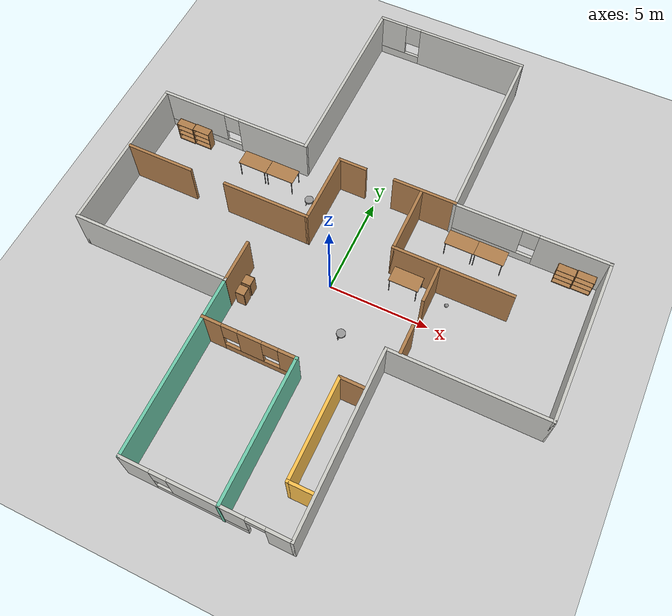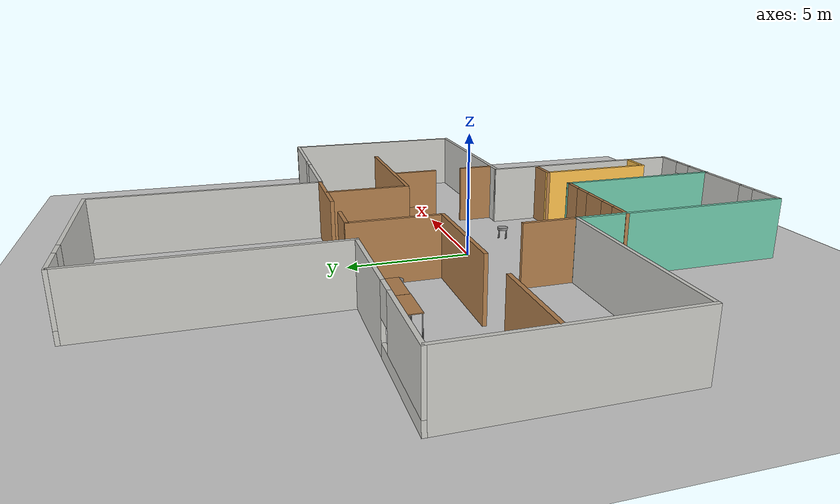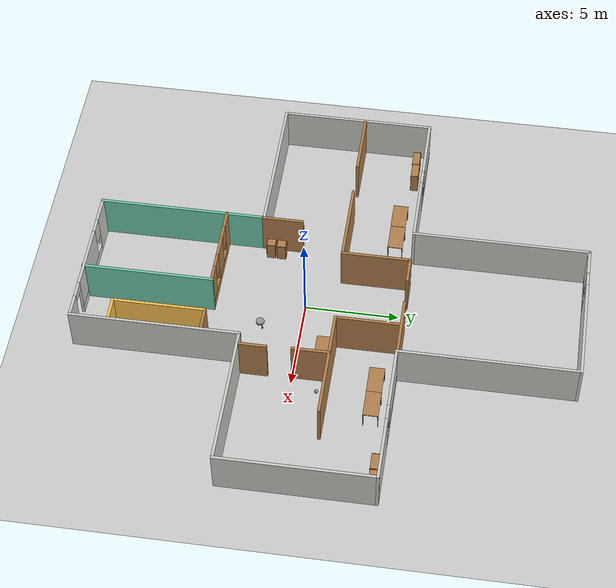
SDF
<sdf version="1.6">
 <world name="default">
  <plugin name="hello" filename="libhello.so"/>
  <light name="sun" type="directional">
   <pose>0 0 10 0 -0 0</pose>
   <diffuse>0.8 0.8 0.8 1</diffuse>
   <specular>0.2 0.2 0.2 1</specular>
   <attenuation>
    <range>1000</range>
    <constant>0.9</constant>
    <linear>0.01</linear>
    <quadratic>0.001</quadratic>
   </attenuation>
   <direction>-0.5 0.1 -0.9</direction>
  </light>
  <model name="ground_plane">
   <static>1</static>
   <link name="link">
    <collision name="collision">
     <geometry><plane><normal>0 0 1</normal><size>100 100</size></plane></geometry>
     <surface>
      <contact><collide_bitmask>65535</collide_bitmask></contact>
      <friction><ode><mu>100</mu><mu2>50</mu2></ode></friction>
     </surface>
    </collision>
    <visual name="visual">
     <cast_shadows>0</cast_shadows>
     <geometry><plane><normal>0 0 1</normal><size>100 100</size></plane></geometry>
     <material>
      <script><uri>file://media/materials/scripts/gazebo.material</uri><name>Gazebo/Grey</name></script>
     </material>
    </visual>
   </link>
  </model>
  <gravity>0 0 -9.8</gravity>
  <magnetic_field>6e-06 2.3e-05 -4.2e-05</magnetic_field>
  <atmosphere type="adiabatic"/>
  <physics name="default_physics" default="0" type="ode">
   <max_step_size>0.001</max_step_size>
   <real_time_factor>1</real_time_factor>
   <real_time_update_rate>1000</real_time_update_rate>
  </physics>
  <scene><ambient>0.4 0.4 0.4 1</ambient><background>0.7 0.7 0.7 1</background><shadows>1</shadows></scene>
  <spherical_coordinates>
   <surface_model>EARTH_WGS84</surface_model>
   <latitude_deg>0</latitude_deg>
   <longitude_deg>0</longitude_deg>
   <elevation>0</elevation>
   <heading_deg>0</heading_deg>
  </spherical_coordinates>
  <model name="model">
   <pose>-0.05674 1.50944 0 0 -0 0</pose>
   <link name="Wall_34">
    <collision name="Wall_34_Collision">
     <geometry><box><size>9.5 0.15 2.5</size></box></geometry>
     <pose>0 0 1.25 0 -0 0</pose>
    </collision>
    <visual name="Wall_34_Visual">
     <pose>0 0 1.25 0 -0 0</pose>
     <geometry><box><size>9.5 0.15 2.5</size></box></geometry>
     <material>
      <script><uri>file://media/materials/scripts/gazebo.material</uri><name>Gazebo/CeilingTiled</name></script>
      <ambient>0.435294 0.796078 0.67451 1</ambient>
     </material>
     <meta><layer>0</layer></meta>
    </visual>
    <pose>-3.8 8.475 0 0 0 -1.5708</pose>
   </link>
   <link name="Wall_35">
    <pose>-7.725 3.8 0 0 -0 3.14159</pose>
    <visual name="Wall_35_Visual_0">
     <pose>-2.11265 0 1.25 0 -0 0</pose>
     <geometry><box><size>3.77469 0.15 2.5</size></box></geometry>
     <material>
      <script><uri>file://media/materials/scripts/gazebo.material</uri><name>Gazebo/CeilingTiled</name></script>
      <ambient>0.435294 0.796078 0.67451 1</ambient>
     </material>
     <meta><layer>0</layer></meta>
    </visual>
    <collision name="Wall_35_Collision_0">
     <geometry><box><size>3.77469 0.15 2.5</size></box></geometry>
     <pose>-2.11265 0 1.25 0 -0 0</pose>
    </collision>
    <visual name="Wall_35_Visual_1">
     <pose>1.88735 0 0.25 0 -0 0</pose>
     <geometry><box><size>4.22531 0.15 0.5</size></box></geometry>
     <material>
      <script><uri>file://media/materials/scripts/gazebo.material</uri><name>Gazebo/CeilingTiled</name></script>
      <ambient>0.435294 0.796078 0.67451 1</ambient>
     </material>
     <meta><layer>0</layer></meta>
    </visual>
    <collision name="Wall_35_Collision_1">
     <geometry><box><size>4.22531 0.15 0.5</size></box></geometry>
     <pose>1.88735 0 0.25 0 -0 0</pose>
    </collision>
    <visual name="Wall_35_Visual_2">
     <pose>2.28735 0 1.5 0 -0 0</pose>
     <geometry><box><size>3.42531 0.15 2</size></box></geometry>
     <material>
      <script><uri>file://media/materials/scripts/gazebo.material</uri><name>Gazebo/CeilingTiled</name></script>
      <ambient>0.435294 0.796078 0.67451 1</ambient>
     </material>
     <meta><layer>0</layer></meta>
    </visual>
    <collision name="Wall_35_Collision_2">
     <geometry><box><size>3.42531 0.15 2</size></box></geometry>
     <pose>2.28735 0 1.5 0 -0 0</pose>
    </collision>
    <visual name="Wall_35_Visual_3">
     <pose>0.174692 0 1.9 0 -0 0</pose>
     <geometry><box><size>0.8 0.15 1.2</size></box></geometry>
     <material>
      <script><uri>file://media/materials/scripts/gazebo.material</uri><name>Gazebo/CeilingTiled</name></script>
      <ambient>0.435294 0.796078 0.67451 1</ambient>
     </material>
     <meta><layer>0</layer></meta>
    </visual>
    <collision name="Wall_35_Collision_3">
     <geometry><box><size>0.8 0.15 1.2</size></box></geometry>
     <pose>0.174692 0 1.9 0 -0 0</pose>
    </collision>
   </link>
   <link name="Wall_36">
    <collision name="Wall_36_Collision">
     <geometry><box><size>8.25 0.15 2.5</size></box></geometry>
     <pose>0 0 1.25 0 -0 0</pose>
    </collision>
    <visual name="Wall_36_Visual">
     <pose>0 0 1.25 0 -0 0</pose>
     <geometry><box><size>8.25 0.15 2.5</size></box></geometry>
     <material>
      <script><uri>file://media/materials/scripts/gazebo.material</uri><name>Gazebo/CeilingTiled</name></script>
      <ambient>0.435294 0.796078 0.67451 1</ambient>
     </material>
     <meta><layer>0</layer></meta>
    </visual>
    <pose>-11.65 -0.25 0 0 0 -1.5708</pose>
   </link>
   <link name="Wall_37">
    <collision name="Wall_37_Collision">
     <geometry><box><size>8 0.15 2.5</size></box></geometry>
     <pose>0 0 1.25 0 -0 0</pose>
    </collision>
    <visual name="Wall_37_Visual">
     <pose>0 0 1.25 0 -0 0</pose>
     <geometry><box><size>8 0.15 2.5</size></box></geometry>
     <material>
      <script><uri>file://media/materials/scripts/gazebo.material</uri><name>Gazebo/CeilingTiled</name></script>
      <ambient>0.435294 0.796078 0.67451 1</ambient>
     </material>
     <meta><layer>0</layer></meta>
    </visual>
    <pose>-7.725 -4.3 0 0 -0 0</pose>
   </link>
   <link name="Wall_38">
    <collision name="Wall_38_Collision">
     <geometry><box><size>9 0.15 2.5</size></box></geometry>
     <pose>0 0 1.25 0 -0 0</pose>
    </collision>
    <visual name="Wall_38_Visual">
     <pose>0 0 1.25 0 -0 0</pose>
     <geometry><box><size>9 0.15 2.5</size></box></geometry>
     <material>
      <script><uri>file://media/materials/scripts/gazebo.material</uri><name>Gazebo/Grey</name></script>
      <ambient>0.435294 0.796078 0.67451 1</ambient>
     </material>
     <meta><layer>0</layer></meta>
    </visual>
    <pose>-3.8 -8.725 0 0 0 -1.5708</pose>
   </link>
   <link name="Wall_39">
    <pose>0.125 -13.15 0 0 -0 0</pose>
    <visual name="Wall_39_Visual_0">
     <pose>-3.25429 0 1.25 0 -0 0</pose>
     <geometry><box><size>1.49142 0.15 2.5</size></box></geometry>
     <material>
      <script><uri>file://media/materials/scripts/gazebo.material</uri><name>Gazebo/CeilingTiled</name></script>
      <ambient>0.435294 0.796078 0.67451 1</ambient>
     </material>
     <meta><layer>0</layer></meta>
    </visual>
    <collision name="Wall_39_Collision_0">
     <geometry><box><size>1.49142 0.15 2.5</size></box></geometry>
     <pose>-3.25429 0 1.25 0 -0 0</pose>
    </collision>
    <visual name="Wall_39_Visual_1">
     <pose>3.3734 0 1.25 0 -0 0</pose>
     <geometry><box><size>1.25321 0.15 2.5</size></box></geometry>
     <material>
      <script><uri>file://media/materials/scripts/gazebo.material</uri><name>Gazebo/CeilingTiled</name></script>
      <ambient>0.435294 0.796078 0.67451 1</ambient>
     </material>
     <meta><layer>0</layer></meta>
    </visual>
    <collision name="Wall_39_Collision_1">
     <geometry><box><size>1.25321 0.15 2.5</size></box></geometry>
     <pose>3.3734 0 1.25 0 -0 0</pose>
    </collision>
    <visual name="Wall_39_Visual_2">
     <pose>-0.330892 0 0.25 0 -0 0</pose>
     <geometry><box><size>4.35537 0.15 0.5</size></box></geometry>
     <material>
      <script><uri>file://media/materials/scripts/gazebo.material</uri><name>Gazebo/CeilingTiled</name></script>
      <ambient>0.435294 0.796078 0.67451 1</ambient>
     </material>
     <meta><layer>0</layer></meta>
    </visual>
    <collision name="Wall_39_Collision_2">
     <geometry><box><size>4.35537 0.15 0.5</size></box></geometry>
     <pose>-0.330892 0 0.25 0 -0 0</pose>
    </collision>
    <visual name="Wall_39_Visual_3">
     <pose>0.069108 0 1.5 0 -0 0</pose>
     <geometry><box><size>3.55537 0.15 2</size></box></geometry>
     <material>
      <script><uri>file://media/materials/scripts/gazebo.material</uri><name>Gazebo/CeilingTiled</name></script>
      <ambient>0.435294 0.796078 0.67451 1</ambient>
     </material>
     <meta><layer>0</layer></meta>
    </visual>
    <collision name="Wall_39_Collision_3">
     <geometry><box><size>3.55537 0.15 2</size></box></geometry>
     <pose>0.069108 0 1.5 0 -0 0</pose>
    </collision>
    <visual name="Wall_39_Visual_4">
     <pose>-2.10858 0 1.9 0 -0 0</pose>
     <geometry><box><size>0.8 0.15 1.2</size></box></geometry>
     <material>
      <script><uri>file://media/materials/scripts/gazebo.material</uri><name>Gazebo/CeilingTiled</name></script>
      <ambient>0.435294 0.796078 0.67451 1</ambient>
     </material>
     <meta><layer>0</layer></meta>
    </visual>
    <collision name="Wall_39_Collision_4">
     <geometry><box><size>0.8 0.15 1.2</size></box></geometry>
     <pose>-2.10858 0 1.9 0 -0 0</pose>
    </collision>
    <visual name="Wall_39_Visual_5">
     <pose>2.29679 0 2.25 0 -0 0</pose>
     <geometry><box><size>0.9 0.15 0.5</size></box></geometry>
     <material>
      <script><uri>file://media/materials/scripts/gazebo.material</uri><name>Gazebo/CeilingTiled</name></script>
      <ambient>0.435294 0.796078 0.67451 1</ambient>
     </material>
     <meta><layer>0</layer></meta>
    </visual>
    <collision name="Wall_39_Collision_5">
     <geometry><box><size>0.9 0.15 0.5</size></box></geometry>
     <pose>2.29679 0 2.25 0 -0 0</pose>
    </collision>
   </link>
   <link name="Wall_40">
    <collision name="Wall_40_Collision">
     <geometry><box><size>9 0.15 2.5</size></box></geometry>
     <pose>0 0 1.25 0 -0 0</pose>
    </collision>
    <visual name="Wall_40_Visual">
     <pose>0 0 1.25 0 -0 0</pose>
     <geometry><box><size>9 0.15 2.5</size></box></geometry>
     <material>
      <script><uri>file://media/materials/scripts/gazebo.material</uri><name>Gazebo/CeilingTiled</name></script>
      <ambient>0.435294 0.796078 0.67451 1</ambient>
     </material>
     <meta><layer>0</layer></meta>
    </visual>
    <pose>4.05 -8.725 0 0 -0 1.5708</pose>
   </link>
   <link name="Wall_41">
    <collision name="Wall_41_Collision">
     <geometry><box><size>7.75 0.15 2.5</size></box></geometry>
     <pose>0 0 1.25 0 -0 0</pose>
    </collision>
    <visual name="Wall_41_Visual">
     <pose>0 0 1.25 0 -0 0</pose>
     <geometry><box><size>7.75 0.15 2.5</size></box></geometry>
     <material>
      <script><uri>file://media/materials/scripts/gazebo.material</uri><name>Gazebo/CeilingTiled</name></script>
      <ambient>0.435294 0.796078 0.67451 1</ambient>
     </material>
     <meta><layer>0</layer></meta>
    </visual>
    <pose>7.85 -4.3 0 0 -0 0</pose>
   </link>
   <link name="Wall_42">
    <collision name="Wall_42_Collision">
     <geometry><box><size>8.25 0.15 2.5</size></box></geometry>
     <pose>0 0 1.25 0 -0 0</pose>
    </collision>
    <visual name="Wall_42_Visual">
     <pose>0 0 1.25 0 -0 0</pose>
     <geometry><box><size>8.25 0.15 2.5</size></box></geometry>
     <material>
      <script><uri>file://media/materials/scripts/gazebo.material</uri><name>Gazebo/CeilingTiled</name></script>
      <ambient>0.435294 0.796078 0.67451 1</ambient>
     </material>
     <meta><layer>0</layer></meta>
    </visual>
    <pose>11.65 -0.25 0 0 -0 1.5708</pose>
   </link>
   <link name="Wall_43">
    <pose>7.85 3.8 0 0 -0 3.14159</pose>
    <visual name="Wall_43_Visual_0">
     <pose>-2.12983 0 1.25 0 -0 0</pose>
     <geometry><box><size>3.49035 0.15 2.5</size></box></geometry>
     <material>
      <script><uri>file://media/materials/scripts/gazebo.material</uri><name>Gazebo/CeilingTiled</name></script>
      <ambient>0.435294 0.796078 0.67451 1</ambient>
     </material>
     <meta><layer>0</layer></meta>
    </visual>
    <collision name="Wall_43_Collision_0">
     <geometry><box><size>3.49035 0.15 2.5</size></box></geometry>
     <pose>-2.12983 0 1.25 0 -0 0</pose>
    </collision>
    <visual name="Wall_43_Visual_1">
     <pose>1.74517 0 0.25 0 -0 0</pose>
     <geometry><box><size>4.25966 0.15 0.5</size></box></geometry>
     <material>
      <script><uri>file://media/materials/scripts/gazebo.material</uri><name>Gazebo/CeilingTiled</name></script>
      <ambient>0.435294 0.796078 0.67451 1</ambient>
     </material>
     <meta><layer>0</layer></meta>
    </visual>
    <collision name="Wall_43_Collision_1">
     <geometry><box><size>4.25966 0.15 0.5</size></box></geometry>
     <pose>1.74517 0 0.25 0 -0 0</pose>
    </collision>
    <visual name="Wall_43_Visual_2">
     <pose>2.14517 0 1.5 0 -0 0</pose>
     <geometry><box><size>3.45966 0.15 2</size></box></geometry>
     <material>
      <script><uri>file://media/materials/scripts/gazebo.material</uri><name>Gazebo/CeilingTiled</name></script>
      <ambient>0.435294 0.796078 0.67451 1</ambient>
     </material>
     <meta><layer>0</layer></meta>
    </visual>
    <collision name="Wall_43_Collision_2">
     <geometry><box><size>3.45966 0.15 2</size></box></geometry>
     <pose>2.14517 0 1.5 0 -0 0</pose>
    </collision>
    <visual name="Wall_43_Visual_3">
     <pose>0.015345 0 1.9 0 -0 0</pose>
     <geometry><box><size>0.8 0.15 1.2</size></box></geometry>
     <material>
      <script><uri>file://media/materials/scripts/gazebo.material</uri><name>Gazebo/CeilingTiled</name></script>
      <ambient>0.435294 0.796078 0.67451 1</ambient>
     </material>
     <meta><layer>0</layer></meta>
    </visual>
    <collision name="Wall_43_Collision_3">
     <geometry><box><size>0.8 0.15 1.2</size></box></geometry>
     <pose>0.015345 0 1.9 0 -0 0</pose>
    </collision>
   </link>
   <link name="Wall_44">
    <collision name="Wall_44_Collision">
     <geometry><box><size>9.5 0.15 2.5</size></box></geometry>
     <pose>0 0 1.25 0 -0 0</pose>
    </collision>
    <visual name="Wall_44_Visual">
     <pose>0 0 1.25 0 -0 0</pose>
     <geometry><box><size>9.5 0.15 2.5</size></box></geometry>
     <material>
      <script><uri>file://media/materials/scripts/gazebo.material</uri><name>Gazebo/CeilingTiled</name></script>
      <ambient>0.435294 0.796078 0.67451 1</ambient>
     </material>
     <meta><layer>0</layer></meta>
    </visual>
    <pose>4.05 8.475 0 0 -0 1.5708</pose>
   </link>
   <link name="Wall_45">
    <pose>0.125 13.15 0 0 -0 3.14159</pose>
    <visual name="Wall_45_Visual_0">
     <pose>-1.14571 0 1.25 0 -0 0</pose>
     <geometry><box><size>5.70858 0.15 2.5</size></box></geometry>
     <material>
      <script><uri>file://media/materials/scripts/gazebo.material</uri><name>Gazebo/CeilingTiled</name></script>
      <ambient>0.435294 0.796078 0.67451 1</ambient>
     </material>
     <meta><layer>0</layer></meta>
    </visual>
    <collision name="Wall_45_Collision_0">
     <geometry><box><size>5.70858 0.15 2.5</size></box></geometry>
     <pose>-1.14571 0 1.25 0 -0 0</pose>
    </collision>
    <visual name="Wall_45_Visual_1">
     <pose>2.85429 0 0.25 0 -0 0</pose>
     <geometry><box><size>2.29142 0.15 0.5</size></box></geometry>
     <material>
      <script><uri>file://media/materials/scripts/gazebo.material</uri><name>Gazebo/CeilingTiled</name></script>
      <ambient>0.435294 0.796078 0.67451 1</ambient>
     </material>
     <meta><layer>0</layer></meta>
    </visual>
    <collision name="Wall_45_Collision_1">
     <geometry><box><size>2.29142 0.15 0.5</size></box></geometry>
     <pose>2.85429 0 0.25 0 -0 0</pose>
    </collision>
    <visual name="Wall_45_Visual_2">
     <pose>3.25429 0 1.5 0 -0 0</pose>
     <geometry><box><size>1.49142 0.15 2</size></box></geometry>
     <material>
      <script><uri>file://media/materials/scripts/gazebo.material</uri><name>Gazebo/CeilingTiled</name></script>
      <ambient>0.435294 0.796078 0.67451 1</ambient>
     </material>
     <meta><layer>0</layer></meta>
    </visual>
    <collision name="Wall_45_Collision_2">
     <geometry><box><size>1.49142 0.15 2</size></box></geometry>
     <pose>3.25429 0 1.5 0 -0 0</pose>
    </collision>
    <visual name="Wall_45_Visual_3">
     <pose>2.10858 0 1.9 0 -0 0</pose>
     <geometry><box><size>0.8 0.15 1.2</size></box></geometry>
     <material>
      <script><uri>file://media/materials/scripts/gazebo.material</uri><name>Gazebo/CeilingTiled</name></script>
      <ambient>0.435294 0.796078 0.67451 1</ambient>
     </material>
     <meta><layer>0</layer></meta>
    </visual>
    <collision name="Wall_45_Collision_3">
     <geometry><box><size>0.8 0.15 1.2</size></box></geometry>
     <pose>2.10858 0 1.9 0 -0 0</pose>
    </collision>
   </link>
   <static>1</static>
  </model>
  <model name="Building"><pose>-20.8921 18.7878 0 0 -0 0</pose><static>1</static></model>
  <model name="table">
   <static>1</static>
   <link name="link">
    <collision name="surface">
     <pose>0 0 1 0 -0 0</pose>
     <geometry><box><size>1.5 0.8 0.03</size></box></geometry>
     <surface><friction><ode><mu>0.6</mu><mu2>0.6</mu2></ode></friction></surface>
    </collision>
    <visual name="visual1">
     <pose>0 0 1 0 -0 0</pose>
     <geometry><box><size>1.5 0.8 0.03</size></box></geometry>
     <material>
      <script><uri>file://media/materials/scripts/gazebo.material</uri><name>Gazebo/Wood</name></script>
     </material>
    </visual>
    <collision name="front_left_leg">
     <pose>0.68 0.38 0.5 0 -0 0</pose>
     <geometry><cylinder><radius>0.02</radius><length>1</length></cylinder></geometry>
    </collision>
    <visual name="front_left_leg">
     <pose>0.68 0.38 0.5 0 -0 0</pose>
     <geometry><cylinder><radius>0.02</radius><length>1</length></cylinder></geometry>
     <material>
      <script><uri>file://media/materials/scripts/gazebo.material</uri><name>Gazebo/Grey</name></script>
     </material>
    </visual>
    <collision name="front_right_leg">
     <pose>0.68 -0.38 0.5 0 -0 0</pose>
     <geometry><cylinder><radius>0.02</radius><length>1</length></cylinder></geometry>
    </collision>
    <visual name="front_right_leg">
     <pose>0.68 -0.38 0.5 0 -0 0</pose>
     <geometry><cylinder><radius>0.02</radius><length>1</length></cylinder></geometry>
     <material>
      <script><uri>file://media/materials/scripts/gazebo.material</uri><name>Gazebo/Grey</name></script>
     </material>
    </visual>
    <collision name="back_right_leg">
     <pose>-0.68 -0.38 0.5 0 -0 0</pose>
     <geometry><cylinder><radius>0.02</radius><length>1</length></cylinder></geometry>
    </collision>
    <visual name="back_right_leg">
     <pose>-0.68 -0.38 0.5 0 -0 0</pose>
     <geometry><cylinder><radius>0.02</radius><length>1</length></cylinder></geometry>
     <material>
      <script><uri>file://media/materials/scripts/gazebo.material</uri><name>Gazebo/Grey</name></script>
     </material>
    </visual>
    <collision name="back_left_leg">
     <pose>-0.68 0.38 0.5 0 -0 0</pose>
     <geometry><cylinder><radius>0.02</radius><length>1</length></cylinder></geometry>
    </collision>
    <visual name="back_left_leg">
     <pose>-0.68 0.38 0.5 0 -0 0</pose>
     <geometry><cylinder><radius>0.02</radius><length>1</length></cylinder></geometry>
     <material>
      <script><uri>file://media/materials/scripts/gazebo.material</uri><name>Gazebo/Grey</name></script>
     </material>
    </visual>
   </link>
   <pose>-6.21534 4.30443 0 0 -0 0</pose>
  </model>
  <model name="table_0">
   <static>1</static>
   <link name="link">
    <collision name="surface">
     <pose>0 0 1 0 -0 0</pose>
     <geometry><box><size>1.5 0.8 0.03</size></box></geometry>
     <surface><friction><ode><mu>0.6</mu><mu2>0.6</mu2></ode></friction></surface>
    </collision>
    <visual name="visual1">
     <pose>0 0 1 0 -0 0</pose>
     <geometry><box><size>1.5 0.8 0.03</size></box></geometry>
     <material>
      <script><uri>file://media/materials/scripts/gazebo.material</uri><name>Gazebo/Wood</name></script>
     </material>
    </visual>
    <collision name="front_left_leg">
     <pose>0.68 0.38 0.5 0 -0 0</pose>
     <geometry><cylinder><radius>0.02</radius><length>1</length></cylinder></geometry>
    </collision>
    <visual name="front_left_leg">
     <pose>0.68 0.38 0.5 0 -0 0</pose>
     <geometry><cylinder><radius>0.02</radius><length>1</length></cylinder></geometry>
     <material>
      <script><uri>file://media/materials/scripts/gazebo.material</uri><name>Gazebo/Grey</name></script>
     </material>
    </visual>
    <collision name="front_right_leg">
     <pose>0.68 -0.38 0.5 0 -0 0</pose>
     <geometry><cylinder><radius>0.02</radius><length>1</length></cylinder></geometry>
    </collision>
    <visual name="front_right_leg">
     <pose>0.68 -0.38 0.5 0 -0 0</pose>
     <geometry><cylinder><radius>0.02</radius><length>1</length></cylinder></geometry>
     <material>
      <script><uri>file://media/materials/scripts/gazebo.material</uri><name>Gazebo/Grey</name></script>
     </material>
    </visual>
    <collision name="back_right_leg">
     <pose>-0.68 -0.38 0.5 0 -0 0</pose>
     <geometry><cylinder><radius>0.02</radius><length>1</length></cylinder></geometry>
    </collision>
    <visual name="back_right_leg">
     <pose>-0.68 -0.38 0.5 0 -0 0</pose>
     <geometry><cylinder><radius>0.02</radius><length>1</length></cylinder></geometry>
     <material>
      <script><uri>file://media/materials/scripts/gazebo.material</uri><name>Gazebo/Grey</name></script>
     </material>
    </visual>
    <collision name="back_left_leg">
     <pose>-0.68 0.38 0.5 0 -0 0</pose>
     <geometry><cylinder><radius>0.02</radius><length>1</length></cylinder></geometry>
    </collision>
    <visual name="back_left_leg">
     <pose>-0.68 0.38 0.5 0 -0 0</pose>
     <geometry><cylinder><radius>0.02</radius><length>1</length></cylinder></geometry>
     <material>
      <script><uri>file://media/materials/scripts/gazebo.material</uri><name>Gazebo/Grey</name></script>
     </material>
    </visual>
   </link>
   <pose>-4.70859 4.31668 0 0 -0 0</pose>
  </model>
  <model name="table_1">
   <static>1</static>
   <link name="link">
    <collision name="surface">
     <pose>0 0 1 0 -0 0</pose>
     <geometry><box><size>1.5 0.8 0.03</size></box></geometry>
     <surface><friction><ode><mu>0.6</mu><mu2>0.6</mu2></ode></friction></surface>
    </collision>
    <visual name="visual1">
     <pose>0 0 1 0 -0 0</pose>
     <geometry><box><size>1.5 0.8 0.03</size></box></geometry>
     <material>
      <script><uri>file://media/materials/scripts/gazebo.material</uri><name>Gazebo/Wood</name></script>
     </material>
    </visual>
    <collision name="front_left_leg">
     <pose>0.68 0.38 0.5 0 -0 0</pose>
     <geometry><cylinder><radius>0.02</radius><length>1</length></cylinder></geometry>
    </collision>
    <visual name="front_left_leg">
     <pose>0.68 0.38 0.5 0 -0 0</pose>
     <geometry><cylinder><radius>0.02</radius><length>1</length></cylinder></geometry>
     <material>
      <script><uri>file://media/materials/scripts/gazebo.material</uri><name>Gazebo/Grey</name></script>
     </material>
    </visual>
    <collision name="front_right_leg">
     <pose>0.68 -0.38 0.5 0 -0 0</pose>
     <geometry><cylinder><radius>0.02</radius><length>1</length></cylinder></geometry>
    </collision>
    <visual name="front_right_leg">
     <pose>0.68 -0.38 0.5 0 -0 0</pose>
     <geometry><cylinder><radius>0.02</radius><length>1</length></cylinder></geometry>
     <material>
      <script><uri>file://media/materials/scripts/gazebo.material</uri><name>Gazebo/Grey</name></script>
     </material>
    </visual>
    <collision name="back_right_leg">
     <pose>-0.68 -0.38 0.5 0 -0 0</pose>
     <geometry><cylinder><radius>0.02</radius><length>1</length></cylinder></geometry>
    </collision>
    <visual name="back_right_leg">
     <pose>-0.68 -0.38 0.5 0 -0 0</pose>
     <geometry><cylinder><radius>0.02</radius><length>1</length></cylinder></geometry>
     <material>
      <script><uri>file://media/materials/scripts/gazebo.material</uri><name>Gazebo/Grey</name></script>
     </material>
    </visual>
    <collision name="back_left_leg">
     <pose>-0.68 0.38 0.5 0 -0 0</pose>
     <geometry><cylinder><radius>0.02</radius><length>1</length></cylinder></geometry>
    </collision>
    <visual name="back_left_leg">
     <pose>-0.68 0.38 0.5 0 -0 0</pose>
     <geometry><cylinder><radius>0.02</radius><length>1</length></cylinder></geometry>
     <material>
      <script><uri>file://media/materials/scripts/gazebo.material</uri><name>Gazebo/Grey</name></script>
     </material>
    </visual>
   </link>
   <pose>4.8801 4.37765 0 0 -0 0</pose>
  </model>
  <model name="table_2">
   <static>1</static>
   <link name="link">
    <collision name="surface">
     <pose>0 0 1 0 -0 0</pose>
     <geometry><box><size>1.5 0.8 0.03</size></box></geometry>
     <surface><friction><ode><mu>0.6</mu><mu2>0.6</mu2></ode></friction></surface>
    </collision>
    <visual name="visual1">
     <pose>0 0 1 0 -0 0</pose>
     <geometry><box><size>1.5 0.8 0.03</size></box></geometry>
     <material>
      <script><uri>file://media/materials/scripts/gazebo.material</uri><name>Gazebo/Wood</name></script>
     </material>
    </visual>
    <collision name="front_left_leg">
     <pose>0.68 0.38 0.5 0 -0 0</pose>
     <geometry><cylinder><radius>0.02</radius><length>1</length></cylinder></geometry>
    </collision>
    <visual name="front_left_leg">
     <pose>0.68 0.38 0.5 0 -0 0</pose>
     <geometry><cylinder><radius>0.02</radius><length>1</length></cylinder></geometry>
     <material>
      <script><uri>file://media/materials/scripts/gazebo.material</uri><name>Gazebo/Grey</name></script>
     </material>
    </visual>
    <collision name="front_right_leg">
     <pose>0.68 -0.38 0.5 0 -0 0</pose>
     <geometry><cylinder><radius>0.02</radius><length>1</length></cylinder></geometry>
    </collision>
    <visual name="front_right_leg">
     <pose>0.68 -0.38 0.5 0 -0 0</pose>
     <geometry><cylinder><radius>0.02</radius><length>1</length></cylinder></geometry>
     <material>
      <script><uri>file://media/materials/scripts/gazebo.material</uri><name>Gazebo/Grey</name></script>
     </material>
    </visual>
    <collision name="back_right_leg">
     <pose>-0.68 -0.38 0.5 0 -0 0</pose>
     <geometry><cylinder><radius>0.02</radius><length>1</length></cylinder></geometry>
    </collision>
    <visual name="back_right_leg">
     <pose>-0.68 -0.38 0.5 0 -0 0</pose>
     <geometry><cylinder><radius>0.02</radius><length>1</length></cylinder></geometry>
     <material>
      <script><uri>file://media/materials/scripts/gazebo.material</uri><name>Gazebo/Grey</name></script>
     </material>
    </visual>
    <collision name="back_left_leg">
     <pose>-0.68 0.38 0.5 0 -0 0</pose>
     <geometry><cylinder><radius>0.02</radius><length>1</length></cylinder></geometry>
    </collision>
    <visual name="back_left_leg">
     <pose>-0.68 0.38 0.5 0 -0 0</pose>
     <geometry><cylinder><radius>0.02</radius><length>1</length></cylinder></geometry>
     <material>
      <script><uri>file://media/materials/scripts/gazebo.material</uri><name>Gazebo/Grey</name></script>
     </material>
    </visual>
   </link>
   <pose>6.3729 4.38661 0 0 -0 0</pose>
  </model>
  <model name="HumanoidRobot_0">
   <link name="link_0">
    <pose>-0 0.009 0.276 0 -0 0</pose>
    <inertial>
     <mass>1</mass>
     <inertia><ixx>0.145833</ixx><ixy>0</ixy><ixz>0</ixz><iyy>0.145833</iyy><iyz>0</iyz><izz>0.125</izz></inertia>
    </inertial>
    <visual name="visual">
     <geometry><cylinder><radius>0.22</radius><length>0.1</length></cylinder></geometry>
     <material>
      <lighting>1</lighting>
      <script><uri>file://media/materials/scripts/gazebo.material</uri><name>Gazebo/Grey</name></script>
      <shader type="pixel"><normal_map>__default__</normal_map></shader>
      <ambient>0.3 0.3 0.3 1</ambient>
      <diffuse>0.7 0.7 0.7 1</diffuse>
      <specular>0.01 0.01 0.01 1</specular>
      <emissive>0 0 0 1</emissive>
     </material>
    </visual>
    <collision name="collision">
     <geometry><cylinder><radius>0.22</radius><length>0.1</length></cylinder></geometry>
     <surface>
      <friction>
       <ode><mu>1</mu><mu2>1</mu2><fdir1>0 0 0</fdir1><slip1>0</slip1><slip2>0</slip2></ode>
       <torsional>
        <coefficient>1</coefficient>
        <patch_radius>0</patch_radius>
        <surface_radius>0</surface_radius>
        <use_patch_radius>1</use_patch_radius>
        <ode><slip>0</slip></ode>
       </torsional>
      </friction>
      <bounce><restitution_coefficient>0</restitution_coefficient><threshold>1e+06</threshold></bounce>
      <contact>
       <collide_without_contact>0</collide_without_contact>
       <collide_without_contact_bitmask>1</collide_without_contact_bitmask>
       <collide_bitmask>1</collide_bitmask>
       <ode>
        <soft_cfm>0</soft_cfm>
        <soft_erp>0.2</soft_erp>
        <kp>1e+13</kp>
        <kd>1</kd>
        <max_vel>0.01</max_vel>
        <min_depth>0</min_depth>
       </ode>
       <bullet>
        <split_impulse>1</split_impulse>
        <split_impulse_penetration_threshold>-0.01</split_impulse_penetration_threshold>
        <soft_cfm>0</soft_cfm>
        <soft_erp>0.2</soft_erp>
        <kp>1e+13</kp>
        <kd>1</kd>
       </bullet>
      </contact>
     </surface>
    </collision>
   </link>
   <link name="link_1">
    <pose>-0.155 -0.0485 0.026 0 -0 0</pose>
    <inertial>
     <mass>1</mass>
     <inertia>
      <ixx>0.166667</ixx>
      <ixy>0</ixy>
      <ixz>0</ixz>
      <iyy>0.166667</iyy>
      <iyz>0</iyz>
      <izz>0.166667</izz>
     </inertia>
    </inertial>
    <visual name="visual">
     <geometry><box><size>0.05 0.05 0.4</size></box></geometry>
     <material>
      <lighting>1</lighting>
      <script><uri>file://media/materials/scripts/gazebo.material</uri><name>Gazebo/Grey</name></script>
      <shader type="pixel"><normal_map>__default__</normal_map></shader>
      <ambient>0.3 0.3 0.3 1</ambient>
      <diffuse>0.7 0.7 0.7 1</diffuse>
      <specular>0.01 0.01 0.01 1</specular>
      <emissive>0 0 0 1</emissive>
     </material>
    </visual>
    <collision name="collision">
     <geometry><box><size>0.05 0.05 0.4</size></box></geometry>
     <surface>
      <friction>
       <ode><mu>1</mu><mu2>1</mu2><fdir1>0 0 0</fdir1><slip1>0</slip1><slip2>0</slip2></ode>
       <torsional>
        <coefficient>1</coefficient>
        <patch_radius>0</patch_radius>
        <surface_radius>0</surface_radius>
        <use_patch_radius>1</use_patch_radius>
        <ode><slip>0</slip></ode>
       </torsional>
      </friction>
      <bounce><restitution_coefficient>0</restitution_coefficient><threshold>1e+06</threshold></bounce>
      <contact>
       <collide_without_contact>0</collide_without_contact>
       <collide_without_contact_bitmask>1</collide_without_contact_bitmask>
       <collide_bitmask>1</collide_bitmask>
       <ode>
        <soft_cfm>0</soft_cfm>
        <soft_erp>0.2</soft_erp>
        <kp>1e+13</kp>
        <kd>1</kd>
        <max_vel>0.01</max_vel>
        <min_depth>0</min_depth>
       </ode>
       <bullet>
        <split_impulse>1</split_impulse>
        <split_impulse_penetration_threshold>-0.01</split_impulse_penetration_threshold>
        <soft_cfm>0</soft_cfm>
        <soft_erp>0.2</soft_erp>
        <kp>1e+13</kp>
        <kd>1</kd>
       </bullet>
      </contact>
     </surface>
    </collision>
   </link>
   <link name="link_1_clone">
    <pose>0.155 0.009 0.026 0 -0 0</pose>
    <inertial>
     <mass>1</mass>
     <inertia>
      <ixx>0.166667</ixx>
      <ixy>0</ixy>
      <ixz>0</ixz>
      <iyy>0.166667</iyy>
      <iyz>0</iyz>
      <izz>0.166667</izz>
     </inertia>
    </inertial>
    <visual name="visual">
     <geometry><box><size>0.05 0.05 0.4</size></box></geometry>
     <material>
      <lighting>1</lighting>
      <script><uri>file://media/materials/scripts/gazebo.material</uri><name>Gazebo/Grey</name></script>
      <shader type="pixel"><normal_map>__default__</normal_map></shader>
      <ambient>0.3 0.3 0.3 1</ambient>
      <diffuse>0.7 0.7 0.7 1</diffuse>
      <specular>0.01 0.01 0.01 1</specular>
      <emissive>0 0 0 1</emissive>
     </material>
    </visual>
    <collision name="collision">
     <geometry><box><size>0.05 0.05 0.4</size></box></geometry>
     <surface>
      <friction>
       <ode><mu>1</mu><mu2>1</mu2><fdir1>0 0 0</fdir1><slip1>0</slip1><slip2>0</slip2></ode>
       <torsional>
        <coefficient>1</coefficient>
        <patch_radius>0</patch_radius>
        <surface_radius>0</surface_radius>
        <use_patch_radius>1</use_patch_radius>
        <ode><slip>0</slip></ode>
       </torsional>
      </friction>
      <bounce><restitution_coefficient>0</restitution_coefficient><threshold>1e+06</threshold></bounce>
      <contact>
       <collide_without_contact>0</collide_without_contact>
       <collide_without_contact_bitmask>1</collide_without_contact_bitmask>
       <collide_bitmask>1</collide_bitmask>
       <ode>
        <soft_cfm>0</soft_cfm>
        <soft_erp>0.2</soft_erp>
        <kp>1e+13</kp>
        <kd>1</kd>
        <max_vel>0.01</max_vel>
        <min_depth>0</min_depth>
       </ode>
       <bullet>
        <split_impulse>1</split_impulse>
        <split_impulse_penetration_threshold>-0.01</split_impulse_penetration_threshold>
        <soft_cfm>0</soft_cfm>
        <soft_erp>0.2</soft_erp>
        <kp>1e+13</kp>
        <kd>1</kd>
       </bullet>
      </contact>
     </surface>
    </collision>
   </link>
   <link name="link_2">
    <pose>-0.155 -0.0135 -0.164 0 -0 0</pose>
    <inertial>
     <mass>1</mass>
     <inertia>
      <ixx>0.166667</ixx>
      <ixy>0</ixy>
      <ixz>0</ixz>
      <iyy>0.166667</iyy>
      <iyz>0</iyz>
      <izz>0.166667</izz>
     </inertia>
    </inertial>
    <visual name="visual">
     <geometry><box><size>0.05 0.12 0.02</size></box></geometry>
     <material>
      <lighting>1</lighting>
      <script><uri>file://media/materials/scripts/gazebo.material</uri><name>Gazebo/Grey</name></script>
      <shader type="pixel"><normal_map>__default__</normal_map></shader>
      <ambient>0.3 0.3 0.3 1</ambient>
      <diffuse>0.7 0.7 0.7 1</diffuse>
      <specular>0.01 0.01 0.01 1</specular>
      <emissive>0 0 0 1</emissive>
     </material>
    </visual>
    <collision name="collision">
     <geometry><box><size>0.05 0.12 0.02</size></box></geometry>
     <surface>
      <friction>
       <ode><mu>1</mu><mu2>1</mu2><fdir1>0 0 0</fdir1><slip1>0</slip1><slip2>0</slip2></ode>
       <torsional>
        <coefficient>1</coefficient>
        <patch_radius>0</patch_radius>
        <surface_radius>0</surface_radius>
        <use_patch_radius>1</use_patch_radius>
        <ode><slip>0</slip></ode>
       </torsional>
      </friction>
      <bounce><restitution_coefficient>0</restitution_coefficient><threshold>1e+06</threshold></bounce>
      <contact>
       <collide_without_contact>0</collide_without_contact>
       <collide_without_contact_bitmask>1</collide_without_contact_bitmask>
       <collide_bitmask>1</collide_bitmask>
       <ode>
        <soft_cfm>0</soft_cfm>
        <soft_erp>0.2</soft_erp>
        <kp>1e+13</kp>
        <kd>1</kd>
        <max_vel>0.01</max_vel>
        <min_depth>0</min_depth>
       </ode>
       <bullet>
        <split_impulse>1</split_impulse>
        <split_impulse_penetration_threshold>-0.01</split_impulse_penetration_threshold>
        <soft_cfm>0</soft_cfm>
        <soft_erp>0.2</soft_erp>
        <kp>1e+13</kp>
        <kd>1</kd>
       </bullet>
      </contact>
     </surface>
    </collision>
   </link>
   <link name="link_2_clone">
    <pose>0.155 0.044 -0.164 0 -0 0</pose>
    <inertial>
     <mass>1</mass>
     <inertia>
      <ixx>0.166667</ixx>
      <ixy>0</ixy>
      <ixz>0</ixz>
      <iyy>0.166667</iyy>
      <iyz>0</iyz>
      <izz>0.166667</izz>
     </inertia>
    </inertial>
    <visual name="visual">
     <geometry><box><size>0.05 0.12 0.02</size></box></geometry>
     <material>
      <lighting>1</lighting>
      <script><uri>file://media/materials/scripts/gazebo.material</uri><name>Gazebo/Grey</name></script>
      <shader type="pixel"><normal_map>__default__</normal_map></shader>
      <ambient>0.3 0.3 0.3 1</ambient>
      <diffuse>0.7 0.7 0.7 1</diffuse>
      <specular>0.01 0.01 0.01 1</specular>
      <emissive>0 0 0 1</emissive>
     </material>
    </visual>
    <collision name="collision">
     <geometry><box><size>0.05 0.12 0.02</size></box></geometry>
     <surface>
      <friction>
       <ode><mu>1</mu><mu2>1</mu2><fdir1>0 0 0</fdir1><slip1>0</slip1><slip2>0</slip2></ode>
       <torsional>
        <coefficient>1</coefficient>
        <patch_radius>0</patch_radius>
        <surface_radius>0</surface_radius>
        <use_patch_radius>1</use_patch_radius>
        <ode><slip>0</slip></ode>
       </torsional>
      </friction>
      <bounce><restitution_coefficient>0</restitution_coefficient><threshold>1e+06</threshold></bounce>
      <contact>
       <collide_without_contact>0</collide_without_contact>
       <collide_without_contact_bitmask>1</collide_without_contact_bitmask>
       <collide_bitmask>1</collide_bitmask>
       <ode>
        <soft_cfm>0</soft_cfm>
        <soft_erp>0.2</soft_erp>
        <kp>1e+13</kp>
        <kd>1</kd>
        <max_vel>0.01</max_vel>
        <min_depth>0</min_depth>
       </ode>
       <bullet>
        <split_impulse>1</split_impulse>
        <split_impulse_penetration_threshold>-0.01</split_impulse_penetration_threshold>
        <soft_cfm>0</soft_cfm>
        <soft_erp>0.2</soft_erp>
        <kp>1e+13</kp>
        <kd>1</kd>
       </bullet>
      </contact>
     </surface>
    </collision>
   </link>
   <joint name="link_0_JOINT_2" type="revolute">
    <parent>link_0</parent>
    <child>link_1</child>
    <axis>
     <xyz>0 0 1</xyz>
     <use_parent_model_frame>0</use_parent_model_frame>
     <limit>
      <lower>-1.79769e+308</lower>
      <upper>1.79769e+308</upper>
      <effort>-1</effort>
      <velocity>-1</velocity>
     </limit>
     <dynamics>
      <spring_reference>0</spring_reference>
      <spring_stiffness>0</spring_stiffness>
      <damping>0</damping>
     </dynamics>
    </axis>
    <physics>
     <ode><limit><cfm>0</cfm><erp>0.2</erp></limit><suspension><cfm>0</cfm><erp>0.2</erp></suspension></ode>
    </physics>
   </joint>
   <joint name="link_0_JOINT_3" type="revolute">
    <parent>link_0</parent>
    <child>link_1_clone</child>
    <axis>
     <xyz>0 0 1</xyz>
     <use_parent_model_frame>0</use_parent_model_frame>
     <limit>
      <lower>-1.79769e+308</lower>
      <upper>1.79769e+308</upper>
      <effort>-1</effort>
      <velocity>-1</velocity>
     </limit>
     <dynamics>
      <spring_reference>0</spring_reference>
      <spring_stiffness>0</spring_stiffness>
      <damping>0</damping>
     </dynamics>
    </axis>
    <physics>
     <ode><limit><cfm>0</cfm><erp>0.2</erp></limit><suspension><cfm>0</cfm><erp>0.2</erp></suspension></ode>
    </physics>
   </joint>
   <joint name="link_1_JOINT_4" type="revolute">
    <parent>link_1</parent>
    <child>link_2</child>
    <axis>
     <xyz>0 0 1</xyz>
     <use_parent_model_frame>0</use_parent_model_frame>
     <limit>
      <lower>-1.79769e+308</lower>
      <upper>1.79769e+308</upper>
      <effort>-1</effort>
      <velocity>-1</velocity>
     </limit>
     <dynamics>
      <spring_reference>0</spring_reference>
      <spring_stiffness>0</spring_stiffness>
      <damping>0</damping>
     </dynamics>
    </axis>
    <physics>
     <ode><limit><cfm>0</cfm><erp>0.2</erp></limit><suspension><cfm>0</cfm><erp>0.2</erp></suspension></ode>
    </physics>
   </joint>
   <joint name="link_1_clone_JOINT_5" type="revolute">
    <parent>link_1_clone</parent>
    <child>link_2_clone</child>
    <axis>
     <xyz>0 0 1</xyz>
     <use_parent_model_frame>0</use_parent_model_frame>
     <limit>
      <lower>-1.79769e+308</lower>
      <upper>1.79769e+308</upper>
      <effort>-1</effort>
      <velocity>-1</velocity>
     </limit>
     <dynamics>
      <spring_reference>0</spring_reference>
      <spring_stiffness>0</spring_stiffness>
      <damping>0</damping>
     </dynamics>
    </axis>
    <physics>
     <ode><limit><cfm>0</cfm><erp>0.2</erp></limit><suspension><cfm>0</cfm><erp>0.2</erp></suspension></ode>
    </physics>
   </joint>
   <static>0</static>
   <pose>1.58283 -2.16705 0.174 -1e-06 1e-06 0.742874</pose>
  </model>
  <model name="HumanoidRobot">
   <link name="link_0">
    <pose>-0 0.009 0.276 0 -0 0</pose>
    <inertial>
     <mass>1</mass>
     <inertia><ixx>0.145833</ixx><ixy>0</ixy><ixz>0</ixz><iyy>0.145833</iyy><iyz>0</iyz><izz>0.125</izz></inertia>
    </inertial>
    <visual name="visual">
     <geometry><cylinder><radius>0.22</radius><length>0.1</length></cylinder></geometry>
     <material>
      <lighting>1</lighting>
      <script><uri>file://media/materials/scripts/gazebo.material</uri><name>Gazebo/Grey</name></script>
      <shader type="pixel"><normal_map>__default__</normal_map></shader>
      <ambient>0.3 0.3 0.3 1</ambient>
      <diffuse>0.7 0.7 0.7 1</diffuse>
      <specular>0.01 0.01 0.01 1</specular>
      <emissive>0 0 0 1</emissive>
     </material>
    </visual>
    <collision name="collision">
     <geometry><cylinder><radius>0.22</radius><length>0.1</length></cylinder></geometry>
     <surface>
      <friction>
       <ode><mu>1</mu><mu2>1</mu2><fdir1>0 0 0</fdir1><slip1>0</slip1><slip2>0</slip2></ode>
       <torsional>
        <coefficient>1</coefficient>
        <patch_radius>0</patch_radius>
        <surface_radius>0</surface_radius>
        <use_patch_radius>1</use_patch_radius>
        <ode><slip>0</slip></ode>
       </torsional>
      </friction>
      <bounce><restitution_coefficient>0</restitution_coefficient><threshold>1e+06</threshold></bounce>
      <contact>
       <collide_without_contact>0</collide_without_contact>
       <collide_without_contact_bitmask>1</collide_without_contact_bitmask>
       <collide_bitmask>1</collide_bitmask>
       <ode>
        <soft_cfm>0</soft_cfm>
        <soft_erp>0.2</soft_erp>
        <kp>1e+13</kp>
        <kd>1</kd>
        <max_vel>0.01</max_vel>
        <min_depth>0</min_depth>
       </ode>
       <bullet>
        <split_impulse>1</split_impulse>
        <split_impulse_penetration_threshold>-0.01</split_impulse_penetration_threshold>
        <soft_cfm>0</soft_cfm>
        <soft_erp>0.2</soft_erp>
        <kp>1e+13</kp>
        <kd>1</kd>
       </bullet>
      </contact>
     </surface>
    </collision>
   </link>
   <link name="link_1">
    <pose>-0.155 -0.0485 0.026 0 -0 0</pose>
    <inertial>
     <mass>1</mass>
     <inertia>
      <ixx>0.166667</ixx>
      <ixy>0</ixy>
      <ixz>0</ixz>
      <iyy>0.166667</iyy>
      <iyz>0</iyz>
      <izz>0.166667</izz>
     </inertia>
    </inertial>
    <visual name="visual">
     <geometry><box><size>0.05 0.05 0.4</size></box></geometry>
     <material>
      <lighting>1</lighting>
      <script><uri>file://media/materials/scripts/gazebo.material</uri><name>Gazebo/Grey</name></script>
      <shader type="pixel"><normal_map>__default__</normal_map></shader>
      <ambient>0.3 0.3 0.3 1</ambient>
      <diffuse>0.7 0.7 0.7 1</diffuse>
      <specular>0.01 0.01 0.01 1</specular>
      <emissive>0 0 0 1</emissive>
     </material>
    </visual>
    <collision name="collision">
     <geometry><box><size>0.05 0.05 0.4</size></box></geometry>
     <surface>
      <friction>
       <ode><mu>1</mu><mu2>1</mu2><fdir1>0 0 0</fdir1><slip1>0</slip1><slip2>0</slip2></ode>
       <torsional>
        <coefficient>1</coefficient>
        <patch_radius>0</patch_radius>
        <surface_radius>0</surface_radius>
        <use_patch_radius>1</use_patch_radius>
        <ode><slip>0</slip></ode>
       </torsional>
      </friction>
      <bounce><restitution_coefficient>0</restitution_coefficient><threshold>1e+06</threshold></bounce>
      <contact>
       <collide_without_contact>0</collide_without_contact>
       <collide_without_contact_bitmask>1</collide_without_contact_bitmask>
       <collide_bitmask>1</collide_bitmask>
       <ode>
        <soft_cfm>0</soft_cfm>
        <soft_erp>0.2</soft_erp>
        <kp>1e+13</kp>
        <kd>1</kd>
        <max_vel>0.01</max_vel>
        <min_depth>0</min_depth>
       </ode>
       <bullet>
        <split_impulse>1</split_impulse>
        <split_impulse_penetration_threshold>-0.01</split_impulse_penetration_threshold>
        <soft_cfm>0</soft_cfm>
        <soft_erp>0.2</soft_erp>
        <kp>1e+13</kp>
        <kd>1</kd>
       </bullet>
      </contact>
     </surface>
    </collision>
   </link>
   <link name="link_1_clone">
    <pose>0.155 0.009 0.026 0 -0 0</pose>
    <inertial>
     <mass>1</mass>
     <inertia>
      <ixx>0.166667</ixx>
      <ixy>0</ixy>
      <ixz>0</ixz>
      <iyy>0.166667</iyy>
      <iyz>0</iyz>
      <izz>0.166667</izz>
     </inertia>
    </inertial>
    <visual name="visual">
     <geometry><box><size>0.05 0.05 0.4</size></box></geometry>
     <material>
      <lighting>1</lighting>
      <script><uri>file://media/materials/scripts/gazebo.material</uri><name>Gazebo/Grey</name></script>
      <shader type="pixel"><normal_map>__default__</normal_map></shader>
      <ambient>0.3 0.3 0.3 1</ambient>
      <diffuse>0.7 0.7 0.7 1</diffuse>
      <specular>0.01 0.01 0.01 1</specular>
      <emissive>0 0 0 1</emissive>
     </material>
    </visual>
    <collision name="collision">
     <geometry><box><size>0.05 0.05 0.4</size></box></geometry>
     <surface>
      <friction>
       <ode><mu>1</mu><mu2>1</mu2><fdir1>0 0 0</fdir1><slip1>0</slip1><slip2>0</slip2></ode>
       <torsional>
        <coefficient>1</coefficient>
        <patch_radius>0</patch_radius>
        <surface_radius>0</surface_radius>
        <use_patch_radius>1</use_patch_radius>
        <ode><slip>0</slip></ode>
       </torsional>
      </friction>
      <bounce><restitution_coefficient>0</restitution_coefficient><threshold>1e+06</threshold></bounce>
      <contact>
       <collide_without_contact>0</collide_without_contact>
       <collide_without_contact_bitmask>1</collide_without_contact_bitmask>
       <collide_bitmask>1</collide_bitmask>
       <ode>
        <soft_cfm>0</soft_cfm>
        <soft_erp>0.2</soft_erp>
        <kp>1e+13</kp>
        <kd>1</kd>
        <max_vel>0.01</max_vel>
        <min_depth>0</min_depth>
       </ode>
       <bullet>
        <split_impulse>1</split_impulse>
        <split_impulse_penetration_threshold>-0.01</split_impulse_penetration_threshold>
        <soft_cfm>0</soft_cfm>
        <soft_erp>0.2</soft_erp>
        <kp>1e+13</kp>
        <kd>1</kd>
       </bullet>
      </contact>
     </surface>
    </collision>
   </link>
   <link name="link_2">
    <pose>-0.155 -0.0135 -0.164 0 -0 0</pose>
    <inertial>
     <mass>1</mass>
     <inertia>
      <ixx>0.166667</ixx>
      <ixy>0</ixy>
      <ixz>0</ixz>
      <iyy>0.166667</iyy>
      <iyz>0</iyz>
      <izz>0.166667</izz>
     </inertia>
    </inertial>
    <visual name="visual">
     <geometry><box><size>0.05 0.12 0.02</size></box></geometry>
     <material>
      <lighting>1</lighting>
      <script><uri>file://media/materials/scripts/gazebo.material</uri><name>Gazebo/Grey</name></script>
      <shader type="pixel"><normal_map>__default__</normal_map></shader>
      <ambient>0.3 0.3 0.3 1</ambient>
      <diffuse>0.7 0.7 0.7 1</diffuse>
      <specular>0.01 0.01 0.01 1</specular>
      <emissive>0 0 0 1</emissive>
     </material>
    </visual>
    <collision name="collision">
     <geometry><box><size>0.05 0.12 0.02</size></box></geometry>
     <surface>
      <friction>
       <ode><mu>1</mu><mu2>1</mu2><fdir1>0 0 0</fdir1><slip1>0</slip1><slip2>0</slip2></ode>
       <torsional>
        <coefficient>1</coefficient>
        <patch_radius>0</patch_radius>
        <surface_radius>0</surface_radius>
        <use_patch_radius>1</use_patch_radius>
        <ode><slip>0</slip></ode>
       </torsional>
      </friction>
      <bounce><restitution_coefficient>0</restitution_coefficient><threshold>1e+06</threshold></bounce>
      <contact>
       <collide_without_contact>0</collide_without_contact>
       <collide_without_contact_bitmask>1</collide_without_contact_bitmask>
       <collide_bitmask>1</collide_bitmask>
       <ode>
        <soft_cfm>0</soft_cfm>
        <soft_erp>0.2</soft_erp>
        <kp>1e+13</kp>
        <kd>1</kd>
        <max_vel>0.01</max_vel>
        <min_depth>0</min_depth>
       </ode>
       <bullet>
        <split_impulse>1</split_impulse>
        <split_impulse_penetration_threshold>-0.01</split_impulse_penetration_threshold>
        <soft_cfm>0</soft_cfm>
        <soft_erp>0.2</soft_erp>
        <kp>1e+13</kp>
        <kd>1</kd>
       </bullet>
      </contact>
     </surface>
    </collision>
   </link>
   <link name="link_2_clone">
    <pose>0.155 0.044 -0.164 0 -0 0</pose>
    <inertial>
     <mass>1</mass>
     <inertia>
      <ixx>0.166667</ixx>
      <ixy>0</ixy>
      <ixz>0</ixz>
      <iyy>0.166667</iyy>
      <iyz>0</iyz>
      <izz>0.166667</izz>
     </inertia>
    </inertial>
    <visual name="visual">
     <geometry><box><size>0.05 0.12 0.02</size></box></geometry>
     <material>
      <lighting>1</lighting>
      <script><uri>file://media/materials/scripts/gazebo.material</uri><name>Gazebo/Grey</name></script>
      <shader type="pixel"><normal_map>__default__</normal_map></shader>
      <ambient>0.3 0.3 0.3 1</ambient>
      <diffuse>0.7 0.7 0.7 1</diffuse>
      <specular>0.01 0.01 0.01 1</specular>
      <emissive>0 0 0 1</emissive>
     </material>
    </visual>
    <collision name="collision">
     <geometry><box><size>0.05 0.12 0.02</size></box></geometry>
     <surface>
      <friction>
       <ode><mu>1</mu><mu2>1</mu2><fdir1>0 0 0</fdir1><slip1>0</slip1><slip2>0</slip2></ode>
       <torsional>
        <coefficient>1</coefficient>
        <patch_radius>0</patch_radius>
        <surface_radius>0</surface_radius>
        <use_patch_radius>1</use_patch_radius>
        <ode><slip>0</slip></ode>
       </torsional>
      </friction>
      <bounce><restitution_coefficient>0</restitution_coefficient><threshold>1e+06</threshold></bounce>
      <contact>
       <collide_without_contact>0</collide_without_contact>
       <collide_without_contact_bitmask>1</collide_without_contact_bitmask>
       <collide_bitmask>1</collide_bitmask>
       <ode>
        <soft_cfm>0</soft_cfm>
        <soft_erp>0.2</soft_erp>
        <kp>1e+13</kp>
        <kd>1</kd>
        <max_vel>0.01</max_vel>
        <min_depth>0</min_depth>
       </ode>
       <bullet>
        <split_impulse>1</split_impulse>
        <split_impulse_penetration_threshold>-0.01</split_impulse_penetration_threshold>
        <soft_cfm>0</soft_cfm>
        <soft_erp>0.2</soft_erp>
        <kp>1e+13</kp>
        <kd>1</kd>
       </bullet>
      </contact>
     </surface>
    </collision>
   </link>
   <joint name="link_0_JOINT_2" type="revolute">
    <parent>link_0</parent>
    <child>link_1</child>
    <axis>
     <xyz>0 0 1</xyz>
     <use_parent_model_frame>0</use_parent_model_frame>
     <limit>
      <lower>-1.79769e+308</lower>
      <upper>1.79769e+308</upper>
      <effort>-1</effort>
      <velocity>-1</velocity>
     </limit>
     <dynamics>
      <spring_reference>0</spring_reference>
      <spring_stiffness>0</spring_stiffness>
      <damping>0</damping>
     </dynamics>
    </axis>
    <physics>
     <ode><limit><cfm>0</cfm><erp>0.2</erp></limit><suspension><cfm>0</cfm><erp>0.2</erp></suspension></ode>
    </physics>
   </joint>
   <joint name="link_0_JOINT_3" type="revolute">
    <parent>link_0</parent>
    <child>link_1_clone</child>
    <axis>
     <xyz>0 0 1</xyz>
     <use_parent_model_frame>0</use_parent_model_frame>
     <limit>
      <lower>-1.79769e+308</lower>
      <upper>1.79769e+308</upper>
      <effort>-1</effort>
      <velocity>-1</velocity>
     </limit>
     <dynamics>
      <spring_reference>0</spring_reference>
      <spring_stiffness>0</spring_stiffness>
      <damping>0</damping>
     </dynamics>
    </axis>
    <physics>
     <ode><limit><cfm>0</cfm><erp>0.2</erp></limit><suspension><cfm>0</cfm><erp>0.2</erp></suspension></ode>
    </physics>
   </joint>
   <joint name="link_1_JOINT_4" type="revolute">
    <parent>link_1</parent>
    <child>link_2</child>
    <axis>
     <xyz>0 0 1</xyz>
     <use_parent_model_frame>0</use_parent_model_frame>
     <limit>
      <lower>-1.79769e+308</lower>
      <upper>1.79769e+308</upper>
      <effort>-1</effort>
      <velocity>-1</velocity>
     </limit>
     <dynamics>
      <spring_reference>0</spring_reference>
      <spring_stiffness>0</spring_stiffness>
      <damping>0</damping>
     </dynamics>
    </axis>
    <physics>
     <ode><limit><cfm>0</cfm><erp>0.2</erp></limit><suspension><cfm>0</cfm><erp>0.2</erp></suspension></ode>
    </physics>
   </joint>
   <joint name="link_1_clone_JOINT_5" type="revolute">
    <parent>link_1_clone</parent>
    <child>link_2_clone</child>
    <axis>
     <xyz>0 0 1</xyz>
     <use_parent_model_frame>0</use_parent_model_frame>
     <limit>
      <lower>-1.79769e+308</lower>
      <upper>1.79769e+308</upper>
      <effort>-1</effort>
      <velocity>-1</velocity>
     </limit>
     <dynamics>
      <spring_reference>0</spring_reference>
      <spring_stiffness>0</spring_stiffness>
      <damping>0</damping>
     </dynamics>
    </axis>
    <physics>
     <ode><limit><cfm>0</cfm><erp>0.2</erp></limit><suspension><cfm>0</cfm><erp>0.2</erp></suspension></ode>
    </physics>
   </joint>
   <static>0</static>
   <pose>-2.94907 3.72429 0.174 -1e-06 1e-06 -2.99311</pose>
  </model>
  <model name="Untitled">
   <pose>-1.7355 -3.158 0 0 -0 0</pose>
   <link name="Wall_11">
    <collision name="Wall_11_Collision">
     <geometry><box><size>3.25 0.15 2.5</size></box></geometry>
     <pose>0 0 1.25 0 -0 0</pose>
    </collision>
    <visual name="Wall_11_Visual">
     <pose>0 0 1.25 0 -0 0</pose>
     <geometry><box><size>3.25 0.15 2.5</size></box></geometry>
     <material>
      <script><uri>file://media/materials/scripts/gazebo.material</uri><name>Gazebo/Wood</name></script>
      <ambient>1 1 1 1</ambient>
     </material>
     <meta><layer>0</layer></meta>
    </visual>
    <pose>4.1755 8.508 0 0 -0 0</pose>
   </link>
   <link name="Wall_13">
    <collision name="Wall_13_Collision">
     <geometry><box><size>3.5 0.15 2.5</size></box></geometry>
     <pose>0 0 1.25 0 -0 0</pose>
    </collision>
    <visual name="Wall_13_Visual">
     <pose>0 0 1.25 0 -0 0</pose>
     <geometry><box><size>3.5 0.15 2.5</size></box></geometry>
     <material>
      <script><uri>file://media/materials/scripts/gazebo.material</uri><name>Gazebo/Wood</name></script>
      <ambient>1 1 1 1</ambient>
     </material>
     <meta><layer>0</layer></meta>
    </visual>
    <pose>4.0285 6.764 0 0 0 -1.5708</pose>
   </link>
   <link name="Wall_14">
    <collision name="Wall_14_Collision">
     <geometry><box><size>6 0.15 2.5</size></box></geometry>
     <pose>0 0 1.25 0 -0 0</pose>
    </collision>
    <visual name="Wall_14_Visual">
     <pose>0 0 1.25 0 -0 0</pose>
     <geometry><box><size>6 0.15 2.5</size></box></geometry>
     <material>
      <script><uri>file://media/materials/scripts/gazebo.material</uri><name>Gazebo/Wood</name></script>
      <ambient>1 1 1 1</ambient>
     </material>
     <meta><layer>0</layer></meta>
    </visual>
    <pose>6.9535 5.089 0 0 -0 0</pose>
   </link>
   <link name="Wall_18">
    <collision name="Wall_18_Collision">
     <geometry><box><size>3.5 0.15 2.5</size></box></geometry>
     <pose>0 0 1.25 0 -0 0</pose>
    </collision>
    <visual name="Wall_18_Visual">
     <pose>0 0 1.25 0 -0 0</pose>
     <geometry><box><size>3.5 0.15 2.5</size></box></geometry>
     <material>
      <script><uri>file://media/materials/scripts/gazebo.material</uri><name>Gazebo/Wood</name></script>
      <ambient>1 1 1 1</ambient>
     </material>
     <meta><layer>0</layer></meta>
    </visual>
    <pose>-8.2035 4.851 0 0 -0 3.14159</pose>
   </link>
   <link name="Wall_22">
    <pose>0.1645 -1.658 0 0 -0 0</pose>
    <visual name="Wall_22_Visual_0">
     <pose>-1.8705 0 1.25 0 -0 0</pose>
     <geometry><box><size>1.009 0.15 2.5</size></box></geometry>
     <material>
      <script><uri>file://media/materials/scripts/gazebo.material</uri><name>Gazebo/Wood</name></script>
      <ambient>1 0.764706 0.305882 1</ambient>
     </material>
     <meta><layer>0</layer></meta>
    </visual>
    <collision name="Wall_22_Collision_0">
     <geometry><box><size>1.009 0.15 2.5</size></box></geometry>
     <pose>-1.8705 0 1.25 0 -0 0</pose>
    </collision>
    <visual name="Wall_22_Visual_1">
     <pose>0.5045 0 0.25 0 -0 0</pose>
     <geometry><box><size>3.741 0.15 0.5</size></box></geometry>
     <material>
      <script><uri>file://media/materials/scripts/gazebo.material</uri><name>Gazebo/Wood</name></script>
      <ambient>1 0.764706 0.305882 1</ambient>
     </material>
     <meta><layer>0</layer></meta>
    </visual>
    <collision name="Wall_22_Collision_1">
     <geometry><box><size>3.741 0.15 0.5</size></box></geometry>
     <pose>0.5045 0 0.25 0 -0 0</pose>
    </collision>
    <visual name="Wall_22_Visual_2">
     <pose>0.023 0 1.5 0 -0 0</pose>
     <geometry><box><size>1.178 0.15 2</size></box></geometry>
     <material>
      <script><uri>file://media/materials/scripts/gazebo.material</uri><name>Gazebo/Wood</name></script>
      <ambient>1 0.764706 0.305882 1</ambient>
     </material>
     <meta><layer>0</layer></meta>
    </visual>
    <collision name="Wall_22_Collision_2">
     <geometry><box><size>1.178 0.15 2</size></box></geometry>
     <pose>0.023 0 1.5 0 -0 0</pose>
    </collision>
    <visual name="Wall_22_Visual_3">
     <pose>1.8935 0 1.5 0 -0 0</pose>
     <geometry><box><size>0.963 0.15 2</size></box></geometry>
     <material>
      <script><uri>file://media/materials/scripts/gazebo.material</uri><name>Gazebo/Wood</name></script>
      <ambient>1 0.764706 0.305882 1</ambient>
     </material>
     <meta><layer>0</layer></meta>
    </visual>
    <collision name="Wall_22_Collision_3">
     <geometry><box><size>0.963 0.15 2</size></box></geometry>
     <pose>1.8935 0 1.5 0 -0 0</pose>
    </collision>
    <visual name="Wall_22_Visual_4">
     <pose>-0.966 0 1.9 0 -0 0</pose>
     <geometry><box><size>0.8 0.15 1.2</size></box></geometry>
     <material>
      <script><uri>file://media/materials/scripts/gazebo.material</uri><name>Gazebo/Wood</name></script>
      <ambient>1 0.764706 0.305882 1</ambient>
     </material>
     <meta><layer>0</layer></meta>
    </visual>
    <collision name="Wall_22_Collision_4">
     <geometry><box><size>0.8 0.15 1.2</size></box></geometry>
     <pose>-0.966 0 1.9 0 -0 0</pose>
    </collision>
    <visual name="Wall_22_Visual_5">
     <pose>1.012 0 1.9 0 -0 0</pose>
     <geometry><box><size>0.8 0.15 1.2</size></box></geometry>
     <material>
      <script><uri>file://media/materials/scripts/gazebo.material</uri><name>Gazebo/Wood</name></script>
      <ambient>1 0.764706 0.305882 1</ambient>
     </material>
     <meta><layer>0</layer></meta>
    </visual>
    <collision name="Wall_22_Collision_5">
     <geometry><box><size>0.8 0.15 1.2</size></box></geometry>
     <pose>1.012 0 1.9 0 -0 0</pose>
    </collision>
   </link>
   <link name="Wall_24">
    <collision name="Wall_24_Collision">
     <geometry><box><size>1.25 0.15 2.5</size></box></geometry>
     <pose>0 0 1.25 0 -0 0</pose>
    </collision>
    <visual name="Wall_24_Visual">
     <pose>0 0 1.25 0 -0 0</pose>
     <geometry><box><size>1.25 0.15 2.5</size></box></geometry>
     <material>
      <script><uri>file://media/materials/scripts/gazebo.material</uri><name>Gazebo/Wood</name></script>
      <ambient>1 1 1 1</ambient>
     </material>
     <meta><layer>0</layer></meta>
    </visual>
    <pose>5.0385 -1.635 0 0 -0 0</pose>
   </link>
   <link name="Wall_26">
    <collision name="Wall_26_Collision">
     <geometry><box><size>2 0.15 2.5</size></box></geometry>
     <pose>0 0 1.25 0 -0 0</pose>
    </collision>
    <visual name="Wall_26_Visual">
     <pose>0 0 1.25 0 -0 0</pose>
     <geometry><box><size>2 0.15 2.5</size></box></geometry>
     <material>
      <script><uri>file://media/materials/scripts/gazebo.material</uri><name>Gazebo/Wood</name></script>
      <ambient>1 1 1 1</ambient>
     </material>
     <meta><layer>0</layer></meta>
    </visual>
    <pose>6.3055 4.133 0 0 0 -1.5708</pose>
   </link>
   <link name="Wall_29">
    <collision name="Wall_29_Collision">
     <geometry><box><size>1.5 0.15 2.5</size></box></geometry>
     <pose>0 0 1.25 0 -0 0</pose>
    </collision>
    <visual name="Wall_29_Visual">
     <pose>0 0 1.25 0 -0 0</pose>
     <geometry><box><size>1.5 0.15 2.5</size></box></geometry>
     <material>
      <script><uri>file://media/materials/scripts/gazebo.material</uri><name>Gazebo/Wood</name></script>
      <ambient>1 1 1 1</ambient>
     </material>
     <meta><layer>0</layer></meta>
    </visual>
    <pose>6.3745 1.163 0 0 0 -1.5708</pose>
   </link>
   <link name="Wall_31">
    <collision name="Wall_31_Collision">
     <geometry><box><size>4.5 0.15 2.5</size></box></geometry>
     <pose>0 0 1.25 0 -0 0</pose>
    </collision>
    <visual name="Wall_31_Visual">
     <pose>0 0 1.25 0 -0 0</pose>
     <geometry><box><size>4.5 0.15 2.5</size></box></geometry>
     <material>
      <script><uri>file://media/materials/scripts/gazebo.material</uri><name>Gazebo/Wood</name></script>
      <ambient>1 1 1 1</ambient>
     </material>
     <meta><layer>0</layer></meta>
    </visual>
    <pose>-2.4445 4.874 0 0 -0 0</pose>
   </link>
   <link name="Wall_32">
    <collision name="Wall_32_Collision">
     <geometry><box><size>3.75 0.15 2.5</size></box></geometry>
     <pose>0 0 1.25 0 -0 0</pose>
    </collision>
    <visual name="Wall_32_Visual">
     <pose>0 0 1.25 0 -0 0</pose>
     <geometry><box><size>3.75 0.15 2.5</size></box></geometry>
     <material>
      <script><uri>file://media/materials/scripts/gazebo.material</uri><name>Gazebo/Wood</name></script>
      <ambient>1 1 1 1</ambient>
     </material>
     <meta><layer>0</layer></meta>
    </visual>
    <pose>-0.2695 6.674 0 0 -0 1.5708</pose>
   </link>
   <link name="Wall_33">
    <collision name="Wall_33_Collision">
     <geometry><box><size>1.5 0.15 2.5</size></box></geometry>
     <pose>0 0 1.25 0 -0 0</pose>
    </collision>
    <visual name="Wall_33_Visual">
     <pose>0 0 1.25 0 -0 0</pose>
     <geometry><box><size>1.5 0.15 2.5</size></box></geometry>
     <material>
      <script><uri>file://media/materials/scripts/gazebo.material</uri><name>Gazebo/Wood</name></script>
      <ambient>1 1 1 1</ambient>
     </material>
     <meta><layer>0</layer></meta>
    </visual>
    <pose>0.4055 8.474 0 0 -0 0</pose>
   </link>
   <link name="Wall_40">
    <collision name="Wall_40_Collision">
     <geometry><box><size>7 0.15 2.5</size></box></geometry>
     <pose>0 0 1.25 0 -0 0</pose>
    </collision>
    <visual name="Wall_40_Visual">
     <pose>0 0 1.25 0 -0 0</pose>
     <geometry><box><size>7 0.15 2.5</size></box></geometry>
     <material>
      <script><uri>file://media/materials/scripts/gazebo.material</uri><name>Gazebo/Grey</name></script>
      <ambient>0.435294 0.796078 0.67451 1</ambient>
     </material>
     <meta><layer>0</layer></meta>
    </visual>
    <pose>2.4645 -5.083 0 0 0 -1.5708</pose>
   </link>
   <link name="Wall_42">
    <collision name="Wall_42_Collision">
     <geometry><box><size>5 0.15 2.5</size></box></geometry>
     <pose>0 0 1.25 0 -0 0</pose>
    </collision>
    <visual name="Wall_42_Visual">
     <pose>0 0 1.25 0 -0 0</pose>
     <geometry><box><size>5 0.15 2.5</size></box></geometry>
     <material>
      <script><uri>file://media/materials/scripts/gazebo.material</uri><name>Gazebo/Grey</name></script>
      <ambient>1 0.764706 0.305882 1</ambient>
     </material>
     <meta><layer>0</layer></meta>
    </visual>
    <pose>4.4885 -4.06 0 0 0 -1.5708</pose>
   </link>
   <link name="Wall_43">
    <collision name="Wall_43_Collision">
     <geometry><box><size>1.25 0.15 2.5</size></box></geometry>
     <pose>0 0 1.25 0 -0 0</pose>
    </collision>
    <visual name="Wall_43_Visual">
     <pose>0 0 1.25 0 -0 0</pose>
     <geometry><box><size>1.25 0.15 2.5</size></box></geometry>
     <material>
      <script><uri>file://media/materials/scripts/gazebo.material</uri><name>Gazebo/Grey</name></script>
      <ambient>1 0.764706 0.305882 1</ambient>
     </material>
     <meta><layer>0</layer></meta>
    </visual>
    <pose>5.0385 -6.485 0 0 -0 0</pose>
   </link>
   <link name="Wall_6">
    <collision name="Wall_6_Collision">
     <geometry><box><size>2.25 0.15 2.5</size></box></geometry>
     <pose>0 0 1.25 0 -0 0</pose>
    </collision>
    <visual name="Wall_6_Visual">
     <pose>0 0 1.25 0 -0 0</pose>
     <geometry><box><size>2.25 0.15 2.5</size></box></geometry>
     <material>
      <script><uri>file://media/materials/scripts/gazebo.material</uri><name>Gazebo/Wood</name></script>
      <ambient>1 1 1 1</ambient>
     </material>
     <meta><layer>0</layer></meta>
    </visual>
    <pose>-2.1125 1.392 0 0 0 -1.5708</pose>
   </link>
   <static>1</static>
  </model>
  <model name="bookshelf">
   <static>1</static>
   <link name="link">
    <inertial><mass>1</mass></inertial>
    <collision name="back">
     <pose>0 0.005 0.6 0 -0 0</pose>
     <geometry><box><size>0.9 0.01 1.2</size></box></geometry>
    </collision>
    <visual name="visual1">
     <pose>0 0.005 0.6 0 -0 0</pose>
     <geometry><box><size>0.9 0.01 1.2</size></box></geometry>
     <material>
      <script><uri>file://media/materials/scripts/gazebo.material</uri><name>Gazebo/Wood</name></script>
     </material>
    </visual>
    <collision name="left_side">
     <pose>0.45 -0.195 0.6 0 -0 0</pose>
     <geometry><box><size>0.02 0.4 1.2</size></box></geometry>
    </collision>
    <visual name="visual2">
     <pose>0.45 -0.195 0.6 0 -0 0</pose>
     <geometry><box><size>0.02 0.4 1.2</size></box></geometry>
     <material>
      <script><uri>file://media/materials/scripts/gazebo.material</uri><name>Gazebo/Wood</name></script>
     </material>
    </visual>
    <collision name="right_side">
     <pose>-0.45 -0.195 0.6 0 -0 0</pose>
     <geometry><box><size>0.02 0.4 1.2</size></box></geometry>
    </collision>
    <visual name="visual3">
     <pose>-0.45 -0.195 0.6 0 -0 0</pose>
     <geometry><box><size>0.02 0.4 1.2</size></box></geometry>
     <material>
      <script><uri>file://media/materials/scripts/gazebo.material</uri><name>Gazebo/Wood</name></script>
     </material>
    </visual>
    <collision name="bottom">
     <pose>0 -0.195 0.03 0 -0 0</pose>
     <geometry><box><size>0.88 0.4 0.06</size></box></geometry>
    </collision>
    <visual name="visual4">
     <pose>0 -0.195 0.03 0 -0 0</pose>
     <geometry><box><size>0.88 0.4 0.06</size></box></geometry>
     <material>
      <script><uri>file://media/materials/scripts/gazebo.material</uri><name>Gazebo/Wood</name></script>
     </material>
    </visual>
    <collision name="top">
     <pose>0 -0.195 1.19 0 -0 0</pose>
     <geometry><box><size>0.88 0.4 0.02</size></box></geometry>
    </collision>
    <visual name="visual5">
     <pose>0 -0.195 1.19 0 -0 0</pose>
     <geometry><box><size>0.88 0.4 0.02</size></box></geometry>
     <material>
      <script><uri>file://media/materials/scripts/gazebo.material</uri><name>Gazebo/Wood</name></script>
     </material>
    </visual>
    <collision name="low_shelf">
     <pose>0 -0.195 0.43 0 -0 0</pose>
     <geometry><box><size>0.88 0.4 0.02</size></box></geometry>
    </collision>
    <visual name="visual6">
     <pose>0 -0.195 0.43 0 -0 0</pose>
     <geometry><box><size>0.88 0.4 0.02</size></box></geometry>
     <material>
      <script><uri>file://media/materials/scripts/gazebo.material</uri><name>Gazebo/Wood</name></script>
     </material>
    </visual>
    <collision name="high_shelf">
     <pose>0 -0.195 0.8 0 -0 0</pose>
     <geometry><box><size>0.88 0.4 0.02</size></box></geometry>
    </collision>
    <visual name="visual7">
     <pose>0 -0.195 0.8 0 -0 0</pose>
     <geometry><box><size>0.88 0.4 0.02</size></box></geometry>
     <material>
      <script><uri>file://media/materials/scripts/gazebo.material</uri><name>Gazebo/Wood</name></script>
     </material>
    </visual>
   </link>
   <pose>9.89649 5.15841 0 0 -0 0</pose>
  </model>
  <model name="bookshelf_0">
   <static>1</static>
   <link name="link">
    <inertial><mass>1</mass></inertial>
    <collision name="back">
     <pose>0 0.005 0.6 0 -0 0</pose>
     <geometry><box><size>0.9 0.01 1.2</size></box></geometry>
    </collision>
    <visual name="visual1">
     <pose>0 0.005 0.6 0 -0 0</pose>
     <geometry><box><size>0.9 0.01 1.2</size></box></geometry>
     <material>
      <script><uri>file://media/materials/scripts/gazebo.material</uri><name>Gazebo/Wood</name></script>
     </material>
    </visual>
    <collision name="left_side">
     <pose>0.45 -0.195 0.6 0 -0 0</pose>
     <geometry><box><size>0.02 0.4 1.2</size></box></geometry>
    </collision>
    <visual name="visual2">
     <pose>0.45 -0.195 0.6 0 -0 0</pose>
     <geometry><box><size>0.02 0.4 1.2</size></box></geometry>
     <material>
      <script><uri>file://media/materials/scripts/gazebo.material</uri><name>Gazebo/Wood</name></script>
     </material>
    </visual>
    <collision name="right_side">
     <pose>-0.45 -0.195 0.6 0 -0 0</pose>
     <geometry><box><size>0.02 0.4 1.2</size></box></geometry>
    </collision>
    <visual name="visual3">
     <pose>-0.45 -0.195 0.6 0 -0 0</pose>
     <geometry><box><size>0.02 0.4 1.2</size></box></geometry>
     <material>
      <script><uri>file://media/materials/scripts/gazebo.material</uri><name>Gazebo/Wood</name></script>
     </material>
    </visual>
    <collision name="bottom">
     <pose>0 -0.195 0.03 0 -0 0</pose>
     <geometry><box><size>0.88 0.4 0.06</size></box></geometry>
    </collision>
    <visual name="visual4">
     <pose>0 -0.195 0.03 0 -0 0</pose>
     <geometry><box><size>0.88 0.4 0.06</size></box></geometry>
     <material>
      <script><uri>file://media/materials/scripts/gazebo.material</uri><name>Gazebo/Wood</name></script>
     </material>
    </visual>
    <collision name="top">
     <pose>0 -0.195 1.19 0 -0 0</pose>
     <geometry><box><size>0.88 0.4 0.02</size></box></geometry>
    </collision>
    <visual name="visual5">
     <pose>0 -0.195 1.19 0 -0 0</pose>
     <geometry><box><size>0.88 0.4 0.02</size></box></geometry>
     <material>
      <script><uri>file://media/materials/scripts/gazebo.material</uri><name>Gazebo/Wood</name></script>
     </material>
    </visual>
    <collision name="low_shelf">
     <pose>0 -0.195 0.43 0 -0 0</pose>
     <geometry><box><size>0.88 0.4 0.02</size></box></geometry>
    </collision>
    <visual name="visual6">
     <pose>0 -0.195 0.43 0 -0 0</pose>
     <geometry><box><size>0.88 0.4 0.02</size></box></geometry>
     <material>
      <script><uri>file://media/materials/scripts/gazebo.material</uri><name>Gazebo/Wood</name></script>
     </material>
    </visual>
    <collision name="high_shelf">
     <pose>0 -0.195 0.8 0 -0 0</pose>
     <geometry><box><size>0.88 0.4 0.02</size></box></geometry>
    </collision>
    <visual name="visual7">
     <pose>0 -0.195 0.8 0 -0 0</pose>
     <geometry><box><size>0.88 0.4 0.02</size></box></geometry>
     <material>
      <script><uri>file://media/materials/scripts/gazebo.material</uri><name>Gazebo/Wood</name></script>
     </material>
    </visual>
   </link>
   <pose>10.8324 5.18126 0 0 -0 0</pose>
  </model>
  <model name="cabinet">
   <static>1</static>
   <link name="cabinet_bottom_plate">
    <inertial>
     <pose>0 0 -1 0 -0 0</pose>
     <inertia><ixx>2.05</ixx><ixy>0</ixy><ixz>0</ixz><iyy>2.05</iyy><iyz>0</iyz><izz>2.05</izz></inertia>
     <mass>25</mass>
    </inertial>
    <collision name="cabinet_bottom_plate_geom">
     <pose>0 0 0.01 0 -0 0</pose>
     <geometry><box><size>0.45 0.45 0.02</size></box></geometry>
    </collision>
    <visual name="cabinet_bottom_plate_geom_visual">
     <pose>0 0 0.01 0 -0 0</pose>
     <geometry><box><size>0.45 0.45 0.02</size></box></geometry>
     <material>
      <script><uri>file://media/materials/scripts/gazebo.material</uri><name>Gazebo/Wood</name></script>
     </material>
    </visual>
    <collision name="cabinet_bottom_plate_geom_cabinet_back_plate">
     <pose>0.235 0 0.51 0 -0 0</pose>
     <geometry><box><size>0.02 0.45 1.02</size></box></geometry>
    </collision>
    <visual name="cabinet_bottom_plate_geom_cabinet_back_plate_visual">
     <pose>0.235 0 0.51 0 -0 0</pose>
     <geometry><box><size>0.02 0.45 1.02</size></box></geometry>
     <material>
      <script><uri>file://media/materials/scripts/gazebo.material</uri><name>Gazebo/Wood</name></script>
     </material>
    </visual>
    <collision name="cabinet_bottom_plate_geom_cabinet_left_plate">
     <pose>0 0.235 0.51 0 -0 0</pose>
     <geometry><box><size>0.45 0.02 1.02</size></box></geometry>
    </collision>
    <visual name="cabinet_bottom_plate_geom_cabinet_left_plate_visual">
     <pose>0 0.235 0.51 0 -0 0</pose>
     <geometry><box><size>0.45 0.02 1.02</size></box></geometry>
     <material>
      <script><uri>file://media/materials/scripts/gazebo.material</uri><name>Gazebo/Wood</name></script>
     </material>
    </visual>
    <collision name="cabinet_bottom_plate_geom_cabinet_middle_plate">
     <pose>0 0 0.51 0 -0 0</pose>
     <geometry><box><size>0.45 0.45 0.02</size></box></geometry>
    </collision>
    <visual name="cabinet_bottom_plate_geom_cabinet_middle_plate_visual">
     <pose>0 0 0.51 0 -0 0</pose>
     <geometry><box><size>0.45 0.45 0.02</size></box></geometry>
     <material>
      <script><uri>file://media/materials/scripts/gazebo.material</uri><name>Gazebo/Wood</name></script>
     </material>
    </visual>
    <collision name="cabinet_bottom_plate_geom_cabinet_right_plate">
     <pose>0 -0.235 0.51 0 -0 0</pose>
     <geometry><box><size>0.45 0.02 1.02</size></box></geometry>
    </collision>
    <visual name="cabinet_bottom_plate_geom_cabinet_right_plate_visual">
     <pose>0 -0.235 0.51 0 -0 0</pose>
     <geometry><box><size>0.45 0.02 1.02</size></box></geometry>
     <material>
      <script><uri>file://media/materials/scripts/gazebo.material</uri><name>Gazebo/Wood</name></script>
     </material>
    </visual>
    <collision name="cabinet_bottom_plate_geom_cabinet_top_plate">
     <pose>0 0 1.01 0 -0 0</pose>
     <geometry><box><size>0.45 0.45 0.02</size></box></geometry>
    </collision>
    <visual name="cabinet_bottom_plate_geom_cabinet_top_plate_visual">
     <pose>0 0 1.01 0 -0 0</pose>
     <geometry><box><size>0.45 0.45 0.02</size></box></geometry>
     <material>
      <script><uri>file://media/materials/scripts/gazebo.material</uri><name>Gazebo/Wood</name></script>
     </material>
    </visual>
   </link>
   <pose>-3.40721 -2.35223 0 0 -0 0</pose>
  </model>
  <model name="cabinet_0">
   <static>1</static>
   <link name="cabinet_bottom_plate">
    <inertial>
     <pose>0 0 -1 0 -0 0</pose>
     <inertia><ixx>2.05</ixx><ixy>0</ixy><ixz>0</ixz><iyy>2.05</iyy><iyz>0</iyz><izz>2.05</izz></inertia>
     <mass>25</mass>
    </inertial>
    <collision name="cabinet_bottom_plate_geom">
     <pose>0 0 0.01 0 -0 0</pose>
     <geometry><box><size>0.45 0.45 0.02</size></box></geometry>
    </collision>
    <visual name="cabinet_bottom_plate_geom_visual">
     <pose>0 0 0.01 0 -0 0</pose>
     <geometry><box><size>0.45 0.45 0.02</size></box></geometry>
     <material>
      <script><uri>file://media/materials/scripts/gazebo.material</uri><name>Gazebo/Wood</name></script>
     </material>
    </visual>
    <collision name="cabinet_bottom_plate_geom_cabinet_back_plate">
     <pose>0.235 0 0.51 0 -0 0</pose>
     <geometry><box><size>0.02 0.45 1.02</size></box></geometry>
    </collision>
    <visual name="cabinet_bottom_plate_geom_cabinet_back_plate_visual">
     <pose>0.235 0 0.51 0 -0 0</pose>
     <geometry><box><size>0.02 0.45 1.02</size></box></geometry>
     <material>
      <script><uri>file://media/materials/scripts/gazebo.material</uri><name>Gazebo/Wood</name></script>
     </material>
    </visual>
    <collision name="cabinet_bottom_plate_geom_cabinet_left_plate">
     <pose>0 0.235 0.51 0 -0 0</pose>
     <geometry><box><size>0.45 0.02 1.02</size></box></geometry>
    </collision>
    <visual name="cabinet_bottom_plate_geom_cabinet_left_plate_visual">
     <pose>0 0.235 0.51 0 -0 0</pose>
     <geometry><box><size>0.45 0.02 1.02</size></box></geometry>
     <material>
      <script><uri>file://media/materials/scripts/gazebo.material</uri><name>Gazebo/Wood</name></script>
     </material>
    </visual>
    <collision name="cabinet_bottom_plate_geom_cabinet_middle_plate">
     <pose>0 0 0.51 0 -0 0</pose>
     <geometry><box><size>0.45 0.45 0.02</size></box></geometry>
    </collision>
    <visual name="cabinet_bottom_plate_geom_cabinet_middle_plate_visual">
     <pose>0 0 0.51 0 -0 0</pose>
     <geometry><box><size>0.45 0.45 0.02</size></box></geometry>
     <material>
      <script><uri>file://media/materials/scripts/gazebo.material</uri><name>Gazebo/Wood</name></script>
     </material>
    </visual>
    <collision name="cabinet_bottom_plate_geom_cabinet_right_plate">
     <pose>0 -0.235 0.51 0 -0 0</pose>
     <geometry><box><size>0.45 0.02 1.02</size></box></geometry>
    </collision>
    <visual name="cabinet_bottom_plate_geom_cabinet_right_plate_visual">
     <pose>0 -0.235 0.51 0 -0 0</pose>
     <geometry><box><size>0.45 0.02 1.02</size></box></geometry>
     <material>
      <script><uri>file://media/materials/scripts/gazebo.material</uri><name>Gazebo/Wood</name></script>
     </material>
    </visual>
    <collision name="cabinet_bottom_plate_geom_cabinet_top_plate">
     <pose>0 0 1.01 0 -0 0</pose>
     <geometry><box><size>0.45 0.45 0.02</size></box></geometry>
    </collision>
    <visual name="cabinet_bottom_plate_geom_cabinet_top_plate_visual">
     <pose>0 0 1.01 0 -0 0</pose>
     <geometry><box><size>0.45 0.45 0.02</size></box></geometry>
     <material>
      <script><uri>file://media/materials/scripts/gazebo.material</uri><name>Gazebo/Wood</name></script>
     </material>
    </visual>
   </link>
   <pose>-3.39336 -1.78509 0 0 -0 0</pose>
  </model>
  <model name="bookshelf_1">
   <static>1</static>
   <link name="link">
    <inertial><mass>1</mass></inertial>
    <collision name="back">
     <pose>0 0.005 0.6 0 -0 0</pose>
     <geometry><box><size>0.9 0.01 1.2</size></box></geometry>
    </collision>
    <visual name="visual1">
     <pose>0 0.005 0.6 0 -0 0</pose>
     <geometry><box><size>0.9 0.01 1.2</size></box></geometry>
     <material>
      <script><uri>file://media/materials/scripts/gazebo.material</uri><name>Gazebo/Wood</name></script>
     </material>
    </visual>
    <collision name="left_side">
     <pose>0.45 -0.195 0.6 0 -0 0</pose>
     <geometry><box><size>0.02 0.4 1.2</size></box></geometry>
    </collision>
    <visual name="visual2">
     <pose>0.45 -0.195 0.6 0 -0 0</pose>
     <geometry><box><size>0.02 0.4 1.2</size></box></geometry>
     <material>
      <script><uri>file://media/materials/scripts/gazebo.material</uri><name>Gazebo/Wood</name></script>
     </material>
    </visual>
    <collision name="right_side">
     <pose>-0.45 -0.195 0.6 0 -0 0</pose>
     <geometry><box><size>0.02 0.4 1.2</size></box></geometry>
    </collision>
    <visual name="visual3">
     <pose>-0.45 -0.195 0.6 0 -0 0</pose>
     <geometry><box><size>0.02 0.4 1.2</size></box></geometry>
     <material>
      <script><uri>file://media/materials/scripts/gazebo.material</uri><name>Gazebo/Wood</name></script>
     </material>
    </visual>
    <collision name="bottom">
     <pose>0 -0.195 0.03 0 -0 0</pose>
     <geometry><box><size>0.88 0.4 0.06</size></box></geometry>
    </collision>
    <visual name="visual4">
     <pose>0 -0.195 0.03 0 -0 0</pose>
     <geometry><box><size>0.88 0.4 0.06</size></box></geometry>
     <material>
      <script><uri>file://media/materials/scripts/gazebo.material</uri><name>Gazebo/Wood</name></script>
     </material>
    </visual>
    <collision name="top">
     <pose>0 -0.195 1.19 0 -0 0</pose>
     <geometry><box><size>0.88 0.4 0.02</size></box></geometry>
    </collision>
    <visual name="visual5">
     <pose>0 -0.195 1.19 0 -0 0</pose>
     <geometry><box><size>0.88 0.4 0.02</size></box></geometry>
     <material>
      <script><uri>file://media/materials/scripts/gazebo.material</uri><name>Gazebo/Wood</name></script>
     </material>
    </visual>
    <collision name="low_shelf">
     <pose>0 -0.195 0.43 0 -0 0</pose>
     <geometry><box><size>0.88 0.4 0.02</size></box></geometry>
    </collision>
    <visual name="visual6">
     <pose>0 -0.195 0.43 0 -0 0</pose>
     <geometry><box><size>0.88 0.4 0.02</size></box></geometry>
     <material>
      <script><uri>file://media/materials/scripts/gazebo.material</uri><name>Gazebo/Wood</name></script>
     </material>
    </visual>
    <collision name="high_shelf">
     <pose>0 -0.195 0.8 0 -0 0</pose>
     <geometry><box><size>0.88 0.4 0.02</size></box></geometry>
    </collision>
    <visual name="visual7">
     <pose>0 -0.195 0.8 0 -0 0</pose>
     <geometry><box><size>0.88 0.4 0.02</size></box></geometry>
     <material>
      <script><uri>file://media/materials/scripts/gazebo.material</uri><name>Gazebo/Wood</name></script>
     </material>
    </visual>
   </link>
   <pose>-9.55689 4.9834 0 0 -0 0</pose>
  </model>
  <model name="bookshelf_2">
   <static>1</static>
   <link name="link">
    <inertial><mass>1</mass></inertial>
    <collision name="back">
     <pose>0 0.005 0.6 0 -0 0</pose>
     <geometry><box><size>0.9 0.01 1.2</size></box></geometry>
    </collision>
    <visual name="visual1">
     <pose>0 0.005 0.6 0 -0 0</pose>
     <geometry><box><size>0.9 0.01 1.2</size></box></geometry>
     <material>
      <script><uri>file://media/materials/scripts/gazebo.material</uri><name>Gazebo/Wood</name></script>
     </material>
    </visual>
    <collision name="left_side">
     <pose>0.45 -0.195 0.6 0 -0 0</pose>
     <geometry><box><size>0.02 0.4 1.2</size></box></geometry>
    </collision>
    <visual name="visual2">
     <pose>0.45 -0.195 0.6 0 -0 0</pose>
     <geometry><box><size>0.02 0.4 1.2</size></box></geometry>
     <material>
      <script><uri>file://media/materials/scripts/gazebo.material</uri><name>Gazebo/Wood</name></script>
     </material>
    </visual>
    <collision name="right_side">
     <pose>-0.45 -0.195 0.6 0 -0 0</pose>
     <geometry><box><size>0.02 0.4 1.2</size></box></geometry>
    </collision>
    <visual name="visual3">
     <pose>-0.45 -0.195 0.6 0 -0 0</pose>
     <geometry><box><size>0.02 0.4 1.2</size></box></geometry>
     <material>
      <script><uri>file://media/materials/scripts/gazebo.material</uri><name>Gazebo/Wood</name></script>
     </material>
    </visual>
    <collision name="bottom">
     <pose>0 -0.195 0.03 0 -0 0</pose>
     <geometry><box><size>0.88 0.4 0.06</size></box></geometry>
    </collision>
    <visual name="visual4">
     <pose>0 -0.195 0.03 0 -0 0</pose>
     <geometry><box><size>0.88 0.4 0.06</size></box></geometry>
     <material>
      <script><uri>file://media/materials/scripts/gazebo.material</uri><name>Gazebo/Wood</name></script>
     </material>
    </visual>
    <collision name="top">
     <pose>0 -0.195 1.19 0 -0 0</pose>
     <geometry><box><size>0.88 0.4 0.02</size></box></geometry>
    </collision>
    <visual name="visual5">
     <pose>0 -0.195 1.19 0 -0 0</pose>
     <geometry><box><size>0.88 0.4 0.02</size></box></geometry>
     <material>
      <script><uri>file://media/materials/scripts/gazebo.material</uri><name>Gazebo/Wood</name></script>
     </material>
    </visual>
    <collision name="low_shelf">
     <pose>0 -0.195 0.43 0 -0 0</pose>
     <geometry><box><size>0.88 0.4 0.02</size></box></geometry>
    </collision>
    <visual name="visual6">
     <pose>0 -0.195 0.43 0 -0 0</pose>
     <geometry><box><size>0.88 0.4 0.02</size></box></geometry>
     <material>
      <script><uri>file://media/materials/scripts/gazebo.material</uri><name>Gazebo/Wood</name></script>
     </material>
    </visual>
    <collision name="high_shelf">
     <pose>0 -0.195 0.8 0 -0 0</pose>
     <geometry><box><size>0.88 0.4 0.02</size></box></geometry>
    </collision>
    <visual name="visual7">
     <pose>0 -0.195 0.8 0 -0 0</pose>
     <geometry><box><size>0.88 0.4 0.02</size></box></geometry>
     <material>
      <script><uri>file://media/materials/scripts/gazebo.material</uri><name>Gazebo/Wood</name></script>
     </material>
    </visual>
   </link>
   <pose>-10.4635 4.95688 0 0 -0 0</pose>
  </model>
  <model name="table_3">
   <static>1</static>
   <link name="link">
    <collision name="surface">
     <pose>0 0 1 0 -0 0</pose>
     <geometry><box><size>1.5 0.8 0.03</size></box></geometry>
     <surface><friction><ode><mu>0.6</mu><mu2>0.6</mu2></ode></friction></surface>
    </collision>
    <visual name="visual1">
     <pose>0 0 1 0 -0 0</pose>
     <geometry><box><size>1.5 0.8 0.03</size></box></geometry>
     <material>
      <script><uri>file://media/materials/scripts/gazebo.material</uri><name>Gazebo/Wood</name></script>
     </material>
    </visual>
    <collision name="front_left_leg">
     <pose>0.68 0.38 0.5 0 -0 0</pose>
     <geometry><cylinder><radius>0.02</radius><length>1</length></cylinder></geometry>
    </collision>
    <visual name="front_left_leg">
     <pose>0.68 0.38 0.5 0 -0 0</pose>
     <geometry><cylinder><radius>0.02</radius><length>1</length></cylinder></geometry>
     <material>
      <script><uri>file://media/materials/scripts/gazebo.material</uri><name>Gazebo/Grey</name></script>
     </material>
    </visual>
    <collision name="front_right_leg">
     <pose>0.68 -0.38 0.5 0 -0 0</pose>
     <geometry><cylinder><radius>0.02</radius><length>1</length></cylinder></geometry>
    </collision>
    <visual name="front_right_leg">
     <pose>0.68 -0.38 0.5 0 -0 0</pose>
     <geometry><cylinder><radius>0.02</radius><length>1</length></cylinder></geometry>
     <material>
      <script><uri>file://media/materials/scripts/gazebo.material</uri><name>Gazebo/Grey</name></script>
     </material>
    </visual>
    <collision name="back_right_leg">
     <pose>-0.68 -0.38 0.5 0 -0 0</pose>
     <geometry><cylinder><radius>0.02</radius><length>1</length></cylinder></geometry>
    </collision>
    <visual name="back_right_leg">
     <pose>-0.68 -0.38 0.5 0 -0 0</pose>
     <geometry><cylinder><radius>0.02</radius><length>1</length></cylinder></geometry>
     <material>
      <script><uri>file://media/materials/scripts/gazebo.material</uri><name>Gazebo/Grey</name></script>
     </material>
    </visual>
    <collision name="back_left_leg">
     <pose>-0.68 0.38 0.5 0 -0 0</pose>
     <geometry><cylinder><radius>0.02</radius><length>1</length></cylinder></geometry>
    </collision>
    <visual name="back_left_leg">
     <pose>-0.68 0.38 0.5 0 -0 0</pose>
     <geometry><cylinder><radius>0.02</radius><length>1</length></cylinder></geometry>
     <material>
      <script><uri>file://media/materials/scripts/gazebo.material</uri><name>Gazebo/Grey</name></script>
     </material>
    </visual>
   </link>
   <pose>3.25778 1.41593 0 0 -0 0</pose>
  </model>
  <model name="my_ball">
   <link name="link_0">
    <inertial>
     <mass>1</mass>
     <inertia><ixx>0.1</ixx><ixy>0</ixy><ixz>0</ixz><iyy>0.1</iyy><iyz>0</iyz><izz>0.1</izz></inertia>
    </inertial>
    <visual name="visual">
     <geometry><sphere><radius>0.1</radius></sphere></geometry>
     <material>
      <lighting>1</lighting>
      <script><uri>file://media/materials/scripts/gazebo.material</uri><name>Gazebo/Grey</name></script>
      <shader type="pixel"><normal_map>__default__</normal_map></shader>
      <ambient>1 1 1 1</ambient>
      <diffuse>1 1 1 1</diffuse>
      <specular>1 1 1 1</specular>
      <emissive>1 1 1 1</emissive>
     </material>
    </visual>
    <collision name="collision">
     <geometry><sphere><radius>0.1</radius></sphere></geometry>
     <surface>
      <friction>
       <ode><mu>1</mu><mu2>1</mu2><fdir1>0 0 0</fdir1><slip1>0</slip1><slip2>0</slip2></ode>
       <torsional>
        <coefficient>1</coefficient>
        <patch_radius>0</patch_radius>
        <surface_radius>0</surface_radius>
        <use_patch_radius>1</use_patch_radius>
        <ode><slip>0</slip></ode>
       </torsional>
      </friction>
      <bounce><restitution_coefficient>0</restitution_coefficient><threshold>1e+06</threshold></bounce>
      <contact>
       <collide_without_contact>0</collide_without_contact>
       <collide_without_contact_bitmask>1</collide_without_contact_bitmask>
       <collide_bitmask>1</collide_bitmask>
       <ode>
        <soft_cfm>0</soft_cfm>
        <soft_erp>0.2</soft_erp>
        <kp>1e+13</kp>
        <kd>1</kd>
        <max_vel>0.01</max_vel>
        <min_depth>0</min_depth>
       </ode>
       <bullet>
        <split_impulse>1</split_impulse>
        <split_impulse_penetration_threshold>-0.01</split_impulse_penetration_threshold>
        <soft_cfm>0</soft_cfm>
        <soft_erp>0.2</soft_erp>
        <kp>1e+13</kp>
        <kd>1</kd>
       </bullet>
      </contact>
     </surface>
    </collision>
   </link>
   <static>0</static>
   <pose>5.38803 1.38591 0.1 0 -0 0</pose>
  </model>
 </world>
</sdf>
